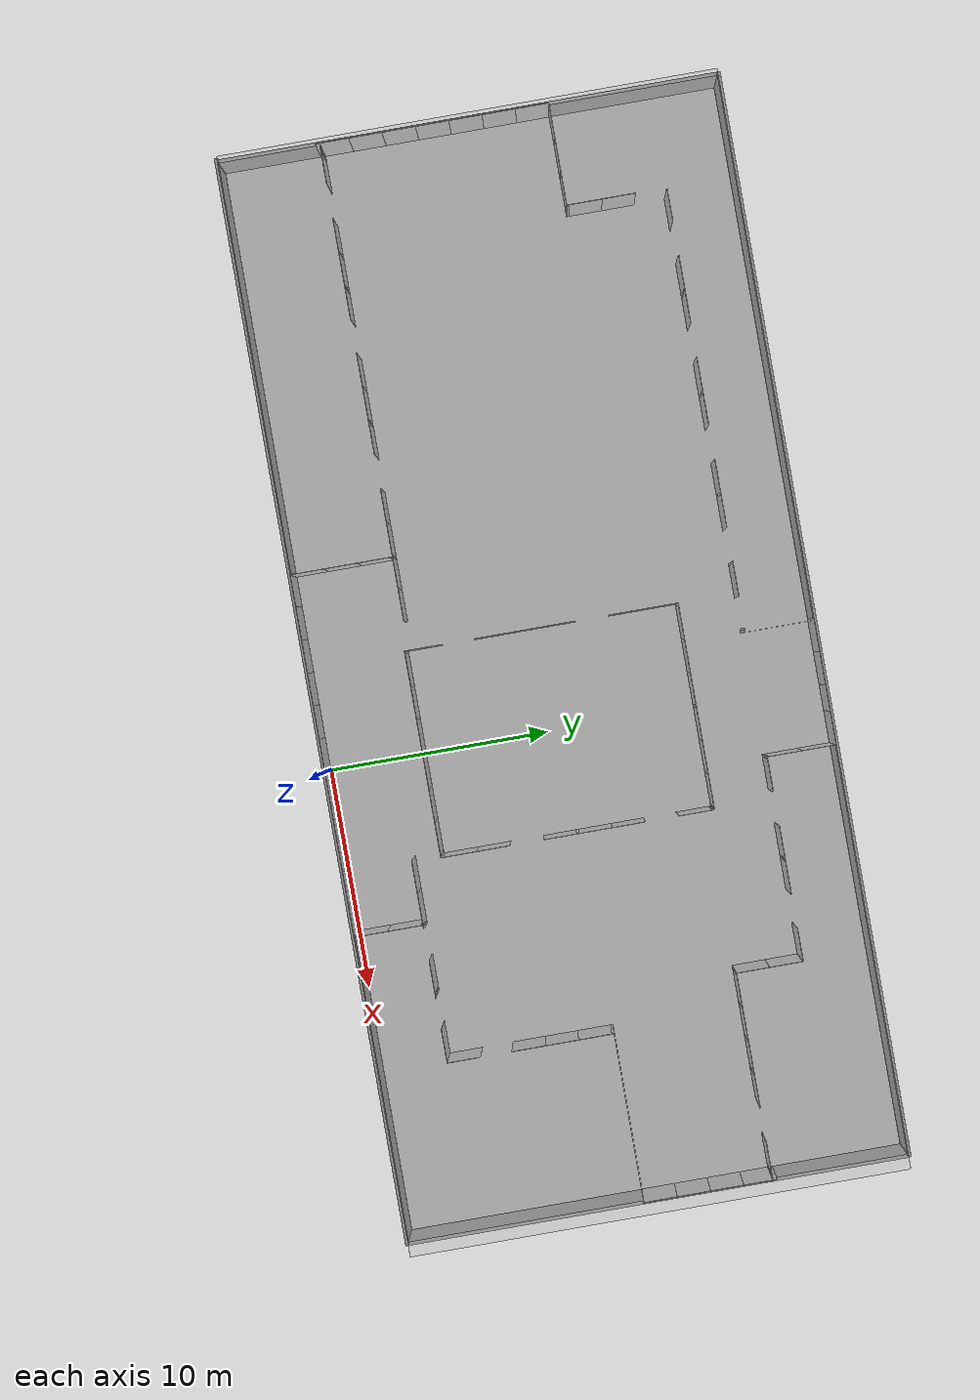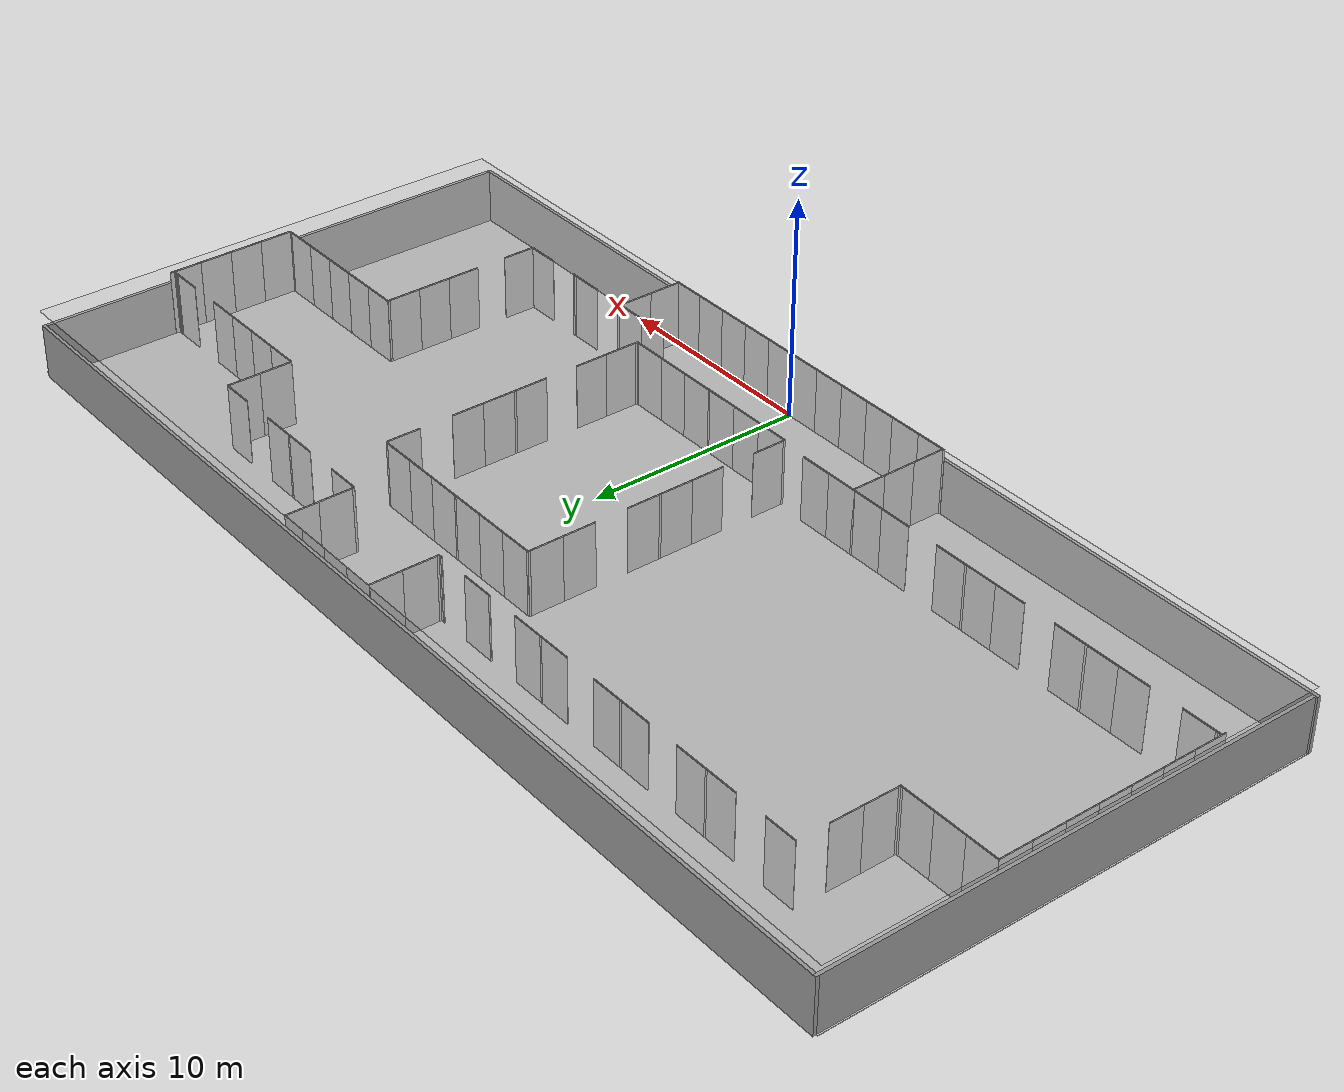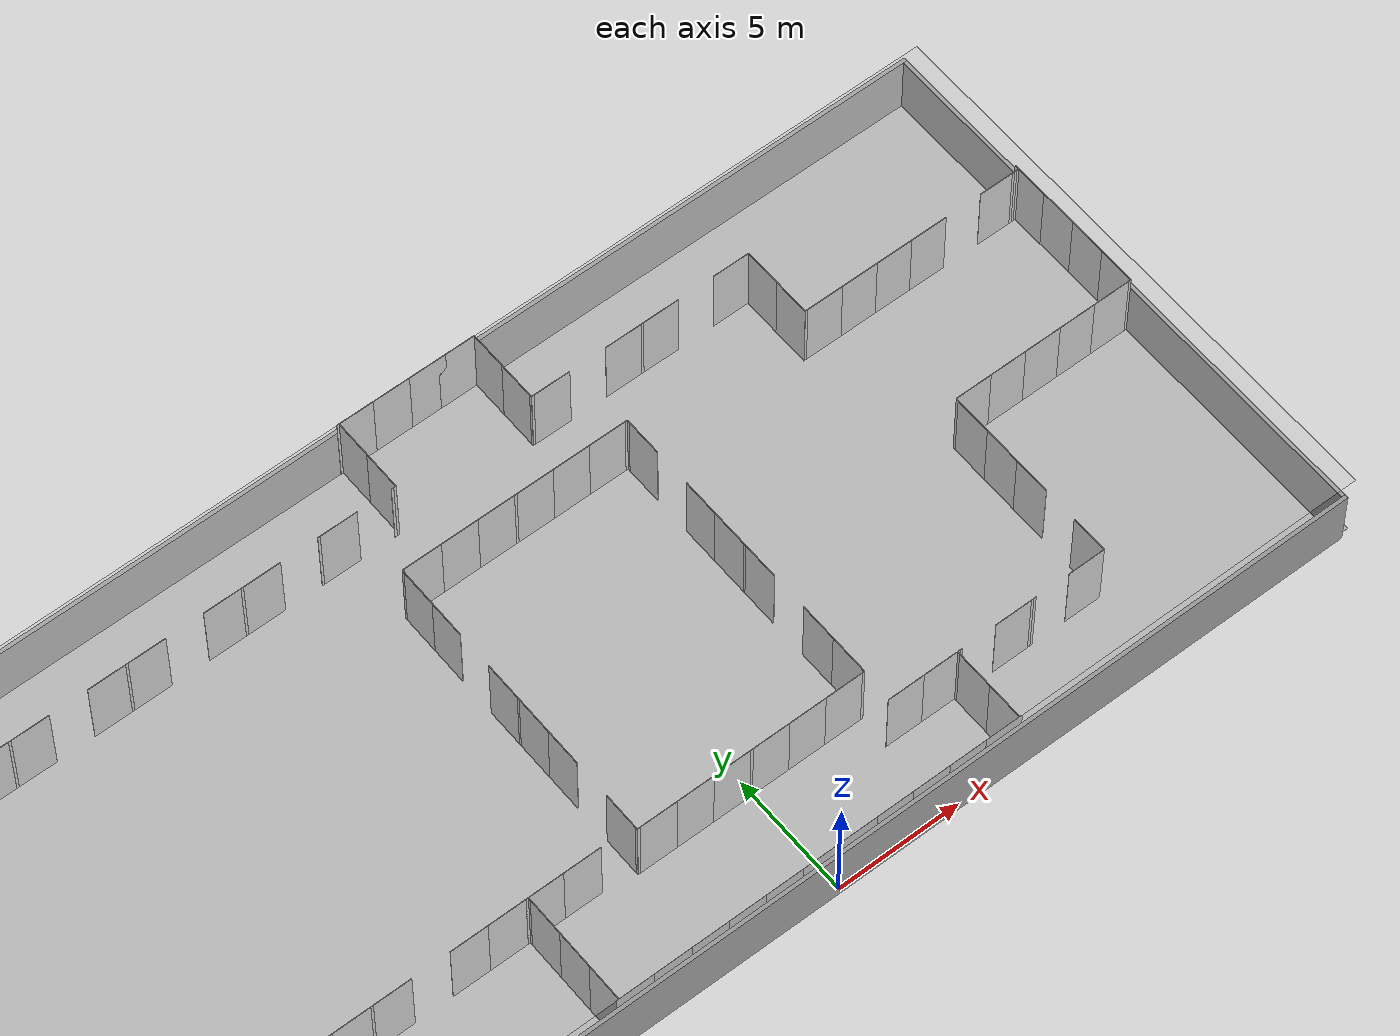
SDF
<sdf version="1.7">
 <world name="default">
  <physics type="ode">
   <real_time_update_rate>500</real_time_update_rate>
   <max_step_size>0.002</max_step_size>
   <real_time_factor>1</real_time_factor>
   <ode>
    <solver>
     <type>quick</type>
     <iters>300</iters>
     <precon_iters>0</precon_iters>
     <sor>1.4</sor>
     <use_dynamic_moi_rescaling>1</use_dynamic_moi_rescaling>
    </solver>
    <constraints>
     <cfm>0</cfm>
     <erp>0.8</erp>
     <contact_max_correcting_vel>2000</contact_max_correcting_vel>
     <contact_surface_layer>0.01</contact_surface_layer>
    </constraints>
   </ode>
  </physics>
  <scene>
   <ambient>0.8 0.8 0.8 1</ambient>
   <background>0.66 0.77 0.84 1</background>
   <grid>0</grid>
   <origin_visual>0</origin_visual>
   <shadows>1</shadows>
  </scene>
  <light name="directional_light" type="directional">
   <pose>0 0 -100 0 -0 0</pose>
   <diffuse>0.5 0.5 0.5 1</diffuse>
   <specular>0.1 0.1 0.1 1</specular>
   <direction>0.1 0.1 -0.9</direction>
   <attenuation>
    <range>20</range>
    <constant>0.5</constant>
    <linear>0.01</linear>
    <quadratic>0.001</quadratic>
   </attenuation>
   <cast_shadows>0</cast_shadows>
   <spot><inner_angle>0</inner_angle><outer_angle>0</outer_angle><falloff>0</falloff></spot>
  </light>
  <model name="ceiling">
   <pose>-2.97 11.25 3 3.14159 -0 3.14159</pose>
   <static>1</static>
   <link name="link">
    <visual name="visual">
     <geometry><plane><normal>0 0 1</normal><size>49.5 22.5</size></plane></geometry>
     <material>
      <script>
       <uri>file://media/materials/scripts/</uri>
       <uri>file://media/materials/textures/</uri>
       <name>ServiceSim/Ceiling</name>
      </script>
     </material>
    </visual>
   </link>
  </model>
  <model name="floor">
   <pose>-2.97 11.25 -0.001 0 -0 0</pose>
   <static>1</static>
   <link name="link">
    <visual name="visual">
     <geometry><plane><normal>0 0 1</normal><size>49.5 22.5</size></plane></geometry>
     <material>
      <script>
       <uri>file://media/materials/scripts/</uri>
       <uri>file://media/materials/textures/</uri>
       <name>ServiceSim/Hallway</name>
      </script>
     </material>
    </visual>
    <collision name="collision">
     <geometry><plane><normal>0 0 1</normal><size>49.5 22.5</size></plane></geometry>
     <surface><friction><ode><mu>1</mu><mu2>1</mu2></ode></friction></surface>
    </collision>
   </link>
  </model>
  <model name="walls">
   <static>1</static>
   <link name="link">
    <visual name="visual_1">
     <pose>-8.25 0 1.5 0 -0 0</pose>
     <geometry><box><size>1.5 0.01 3</size></box></geometry>
     <material>
      <script>
       <uri>file://media/materials/scripts/</uri>
       <uri>file://media/materials/textures/</uri>
       <name>ServiceSim/PlainWall</name>
      </script>
     </material>
    </visual>
    <collision name="collision_1">
     <pose>-8.25 0 1.5 0 -0 0</pose>
     <geometry><box><size>1.5 0.01 3</size></box></geometry>
    </collision>
    <visual name="visual_2">
     <pose>-6.75 0 1.5 0 -0 0</pose>
     <geometry><box><size>1.5 0.01 3</size></box></geometry>
     <material>
      <script>
       <uri>file://media/materials/scripts/</uri>
       <uri>file://media/materials/textures/</uri>
       <name>ServiceSim/PlainWall</name>
      </script>
     </material>
    </visual>
    <collision name="collision_2">
     <pose>-6.75 0 1.5 0 -0 0</pose>
     <geometry><box><size>1.5 0.01 3</size></box></geometry>
    </collision>
    <visual name="visual_3">
     <pose>-5.25 0 1.5 0 -0 0</pose>
     <geometry><box><size>1.5 0.01 3</size></box></geometry>
     <material>
      <script>
       <uri>file://media/materials/scripts/</uri>
       <uri>file://media/materials/textures/</uri>
       <name>ServiceSim/PlainWall</name>
      </script>
     </material>
    </visual>
    <collision name="collision_3">
     <pose>-5.25 0 1.5 0 -0 0</pose>
     <geometry><box><size>1.5 0.01 3</size></box></geometry>
    </collision>
    <visual name="visual_4">
     <pose>-3.75 0 1.5 0 -0 0</pose>
     <geometry><box><size>1.5 0.01 3</size></box></geometry>
     <material>
      <script>
       <uri>file://media/materials/scripts/</uri>
       <uri>file://media/materials/textures/</uri>
       <name>ServiceSim/PlainWall</name>
      </script>
     </material>
    </visual>
    <collision name="collision_4">
     <pose>-3.75 0 1.5 0 -0 0</pose>
     <geometry><box><size>1.5 0.01 3</size></box></geometry>
    </collision>
    <visual name="visual_5">
     <pose>-2.25 0 1.5 0 -0 0</pose>
     <geometry><box><size>1.5 0.01 3</size></box></geometry>
     <material>
      <script>
       <uri>file://media/materials/scripts/</uri>
       <uri>file://media/materials/textures/</uri>
       <name>ServiceSim/PlainWall</name>
      </script>
     </material>
    </visual>
    <collision name="collision_5">
     <pose>-2.25 0 1.5 0 -0 0</pose>
     <geometry><box><size>1.5 0.01 3</size></box></geometry>
    </collision>
    <visual name="visual_6">
     <pose>-0.75 0 1.5 0 -0 0</pose>
     <geometry><box><size>1.5 0.01 3</size></box></geometry>
     <material>
      <script>
       <uri>file://media/materials/scripts/</uri>
       <uri>file://media/materials/textures/</uri>
       <name>ServiceSim/Elevator</name>
      </script>
     </material>
    </visual>
    <collision name="collision_6">
     <pose>-0.75 0 1.5 0 -0 0</pose>
     <geometry><box><size>1.5 0.01 3</size></box></geometry>
    </collision>
    <visual name="visual_7">
     <pose>0.75 0 1.5 0 -0 0</pose>
     <geometry><box><size>1.5 0.01 3</size></box></geometry>
     <material>
      <script>
       <uri>file://media/materials/scripts/</uri>
       <uri>file://media/materials/textures/</uri>
       <name>ServiceSim/Elevator</name>
      </script>
     </material>
    </visual>
    <collision name="collision_7">
     <pose>0.75 0 1.5 0 -0 0</pose>
     <geometry><box><size>1.5 0.01 3</size></box></geometry>
    </collision>
    <visual name="visual_8">
     <pose>2.25 0 1.5 0 -0 0</pose>
     <geometry><box><size>1.5 0.01 3</size></box></geometry>
     <material>
      <script>
       <uri>file://media/materials/scripts/</uri>
       <uri>file://media/materials/textures/</uri>
       <name>ServiceSim/PlainWall</name>
      </script>
     </material>
    </visual>
    <collision name="collision_8">
     <pose>2.25 0 1.5 0 -0 0</pose>
     <geometry><box><size>1.5 0.01 3</size></box></geometry>
    </collision>
    <visual name="visual_9">
     <pose>3.75 0 1.5 0 -0 0</pose>
     <geometry><box><size>1.5 0.01 3</size></box></geometry>
     <material>
      <script>
       <uri>file://media/materials/scripts/</uri>
       <uri>file://media/materials/textures/</uri>
       <name>ServiceSim/PlainWall</name>
      </script>
     </material>
    </visual>
    <collision name="collision_9">
     <pose>3.75 0 1.5 0 -0 0</pose>
     <geometry><box><size>1.5 0.01 3</size></box></geometry>
    </collision>
    <visual name="visual_10">
     <pose>5.25 0 1.5 0 -0 0</pose>
     <geometry><box><size>1.5 0.01 3</size></box></geometry>
     <material>
      <script>
       <uri>file://media/materials/scripts/</uri>
       <uri>file://media/materials/textures/</uri>
       <name>ServiceSim/PlainWall</name>
      </script>
     </material>
    </visual>
    <collision name="collision_10">
     <pose>5.25 0 1.5 0 -0 0</pose>
     <geometry><box><size>1.5 0.01 3</size></box></geometry>
    </collision>
    <visual name="visual_11">
     <pose>6.749 0 1.5 0 -0 0</pose>
     <geometry><box><size>1.5 0.01 3</size></box></geometry>
     <material>
      <script>
       <uri>file://media/materials/scripts/</uri>
       <uri>file://media/materials/textures/</uri>
       <name>ServiceSim/PlainWall</name>
      </script>
     </material>
    </visual>
    <collision name="collision_11">
     <pose>6.749 0 1.5 0 -0 0</pose>
     <geometry><box><size>1.5 0.01 3</size></box></geometry>
    </collision>
    <visual name="visual_12">
     <pose>-8.25 4.6 1.5 0 -0 0</pose>
     <geometry><box><size>1.5 0.01 3</size></box></geometry>
     <material>
      <script>
       <uri>file://media/materials/scripts/</uri>
       <uri>file://media/materials/textures/</uri>
       <name>ServiceSim/PlainWall</name>
      </script>
     </material>
    </visual>
    <collision name="collision_12">
     <pose>-8.25 4.6 1.5 0 -0 0</pose>
     <geometry><box><size>1.5 0.01 3</size></box></geometry>
    </collision>
    <visual name="visual_13">
     <pose>-6.75 4.6 1.5 0 -0 0</pose>
     <geometry><box><size>1.5 0.01 3</size></box></geometry>
     <material>
      <script>
       <uri>file://media/materials/scripts/</uri>
       <uri>file://media/materials/textures/</uri>
       <name>ServiceSim/PlainWall</name>
      </script>
     </material>
    </visual>
    <collision name="collision_13">
     <pose>-6.75 4.6 1.5 0 -0 0</pose>
     <geometry><box><size>1.5 0.01 3</size></box></geometry>
    </collision>
    <visual name="visual_14">
     <pose>5.25 3.1 1.5 0 -0 0</pose>
     <geometry><box><size>1.5 0.01 3</size></box></geometry>
     <material>
      <script>
       <uri>file://media/materials/scripts/</uri>
       <uri>file://media/materials/textures/</uri>
       <name>ServiceSim/PlainWall</name>
      </script>
     </material>
    </visual>
    <collision name="collision_14">
     <pose>5.25 3.1 1.5 0 -0 0</pose>
     <geometry><box><size>1.5 0.01 3</size></box></geometry>
    </collision>
    <visual name="visual_15">
     <pose>6.75 3.1 1.5 0 -0 0</pose>
     <geometry><box><size>1.5 0.01 3</size></box></geometry>
     <material>
      <script>
       <uri>file://media/materials/scripts/</uri>
       <uri>file://media/materials/textures/</uri>
       <name>ServiceSim/PlainWall</name>
      </script>
     </material>
    </visual>
    <collision name="collision_15">
     <pose>6.75 3.1 1.5 0 -0 0</pose>
     <geometry><box><size>1.5 0.01 3</size></box></geometry>
    </collision>
    <visual name="visual_16">
     <pose>7.4 0.75 1.5 0 -0 1.5708</pose>
     <geometry><box><size>1.5 0.01 3</size></box></geometry>
     <material>
      <script>
       <uri>file://media/materials/scripts/</uri>
       <uri>file://media/materials/textures/</uri>
       <name>ServiceSim/PlainWall</name>
      </script>
     </material>
    </visual>
    <collision name="collision_16">
     <pose>7.4 0.75 1.5 0 -0 1.5708</pose>
     <geometry><box><size>1.5 0.01 3</size></box></geometry>
    </collision>
    <visual name="visual_17">
     <pose>7.4 2.25 1.5 0 -0 1.5708</pose>
     <geometry><box><size>1.5 0.01 3</size></box></geometry>
     <material>
      <script>
       <uri>file://media/materials/scripts/</uri>
       <uri>file://media/materials/textures/</uri>
       <name>ServiceSim/PlainWall</name>
      </script>
     </material>
    </visual>
    <collision name="collision_17">
     <pose>7.4 2.25 1.5 0 -0 1.5708</pose>
     <geometry><box><size>1.5 0.01 3</size></box></geometry>
    </collision>
    <visual name="visual_18">
     <pose>7.4 3.05 1.5 0 -0 1.5708</pose>
     <geometry><box><size>0.1 0.01 3</size></box></geometry>
     <material>
      <script>
       <uri>file://media/materials/scripts/</uri>
       <uri>file://media/materials/textures/</uri>
       <name>ServiceSim/PlainWall</name>
      </script>
     </material>
    </visual>
    <collision name="collision_18">
     <pose>7.4 3.05 1.5 0 -0 1.5708</pose>
     <geometry><box><size>0.1 0.01 3</size></box></geometry>
    </collision>
    <visual name="visual_19">
     <pose>7.45 3.1 1.5 0 -0 0</pose>
     <geometry><box><size>0.1 0.01 3</size></box></geometry>
     <material>
      <script>
       <uri>file://media/materials/scripts/</uri>
       <uri>file://media/materials/textures/</uri>
       <name>ServiceSim/PlainWall</name>
      </script>
     </material>
    </visual>
    <collision name="collision_19">
     <pose>7.45 3.1 1.5 0 -0 0</pose>
     <geometry><box><size>0.1 0.01 3</size></box></geometry>
    </collision>
    <visual name="visual_20">
     <pose>7.55 3.1 1.5 0 -0 0</pose>
     <geometry><box><size>0.1 0.01 3</size></box></geometry>
     <material>
      <script>
       <uri>file://media/materials/scripts/</uri>
       <uri>file://media/materials/textures/</uri>
       <name>ServiceSim/PlainWall</name>
      </script>
     </material>
    </visual>
    <collision name="collision_20">
     <pose>7.55 3.1 1.5 0 -0 0</pose>
     <geometry><box><size>0.1 0.01 3</size></box></geometry>
    </collision>
    <visual name="visual_21">
     <pose>9.75 3.1 1.5 0 -0 0</pose>
     <geometry><box><size>1.5 0.01 3</size></box></geometry>
     <material>
      <script>
       <uri>file://media/materials/scripts/</uri>
       <uri>file://media/materials/textures/</uri>
       <name>ServiceSim/PlainWall</name>
      </script>
     </material>
    </visual>
    <collision name="collision_21">
     <pose>9.75 3.1 1.5 0 -0 0</pose>
     <geometry><box><size>1.5 0.01 3</size></box></geometry>
    </collision>
    <visual name="visual_22">
     <pose>10.55 3.1 1.5 0 -0 0</pose>
     <geometry><box><size>0.1 0.01 3</size></box></geometry>
     <material>
      <script>
       <uri>file://media/materials/scripts/</uri>
       <uri>file://media/materials/textures/</uri>
       <name>ServiceSim/PlainWall</name>
      </script>
     </material>
    </visual>
    <collision name="collision_22">
     <pose>10.55 3.1 1.5 0 -0 0</pose>
     <geometry><box><size>0.1 0.01 3</size></box></geometry>
    </collision>
    <visual name="visual_23">
     <pose>10.65 3.1 1.5 0 -0 0</pose>
     <geometry><box><size>0.1 0.01 3</size></box></geometry>
     <material>
      <script>
       <uri>file://media/materials/scripts/</uri>
       <uri>file://media/materials/textures/</uri>
       <name>ServiceSim/PlainWall</name>
      </script>
     </material>
    </visual>
    <collision name="collision_23">
     <pose>10.65 3.1 1.5 0 -0 0</pose>
     <geometry><box><size>0.1 0.01 3</size></box></geometry>
    </collision>
    <visual name="visual_24">
     <pose>12.85 3.1 1.5 0 -0 0</pose>
     <geometry><box><size>1.5 0.01 3</size></box></geometry>
     <material>
      <script>
       <uri>file://media/materials/scripts/</uri>
       <uri>file://media/materials/textures/</uri>
       <name>ServiceSim/PlainWall</name>
      </script>
     </material>
    </visual>
    <collision name="collision_24">
     <pose>12.85 3.1 1.5 0 -0 0</pose>
     <geometry><box><size>1.5 0.01 3</size></box></geometry>
    </collision>
    <visual name="visual_25">
     <pose>13.6 3.85 1.5 0 -0 1.5708</pose>
     <geometry><box><size>1.5 0.01 3</size></box></geometry>
     <material>
      <script>
       <uri>file://media/materials/scripts/</uri>
       <uri>file://media/materials/textures/</uri>
       <name>ServiceSim/PlainWall</name>
      </script>
     </material>
    </visual>
    <collision name="collision_25">
     <pose>13.6 3.85 1.5 0 -0 1.5708</pose>
     <geometry><box><size>1.5 0.01 3</size></box></geometry>
    </collision>
    <visual name="visual_26">
     <pose>13.6 6.75 1.5 0 -0 1.5708</pose>
     <geometry><box><size>1.5 0.01 3</size></box></geometry>
     <material>
      <script>
       <uri>file://media/materials/scripts/</uri>
       <uri>file://media/materials/textures/</uri>
       <name>ServiceSim/PlainWall</name>
      </script>
     </material>
    </visual>
    <collision name="collision_26">
     <pose>13.6 6.75 1.5 0 -0 1.5708</pose>
     <geometry><box><size>1.5 0.01 3</size></box></geometry>
    </collision>
    <visual name="visual_27">
     <pose>13.6 8.25 1.5 0 -0 1.5708</pose>
     <geometry><box><size>1.5 0.01 3</size></box></geometry>
     <material>
      <script>
       <uri>file://media/materials/scripts/</uri>
       <uri>file://media/materials/textures/</uri>
       <name>ServiceSim/PlainWall</name>
      </script>
     </material>
    </visual>
    <collision name="collision_27">
     <pose>13.6 8.25 1.5 0 -0 1.5708</pose>
     <geometry><box><size>1.5 0.01 3</size></box></geometry>
    </collision>
    <visual name="visual_28">
     <pose>13.6 9.75 1.5 0 -0 1.5708</pose>
     <geometry><box><size>1.5 0.01 3</size></box></geometry>
     <material>
      <script>
       <uri>file://media/materials/scripts/</uri>
       <uri>file://media/materials/textures/</uri>
       <name>ServiceSim/PlainWall</name>
      </script>
     </material>
    </visual>
    <collision name="collision_28">
     <pose>13.6 9.75 1.5 0 -0 1.5708</pose>
     <geometry><box><size>1.5 0.01 3</size></box></geometry>
    </collision>
    <visual name="visual_29">
     <pose>13.6 10.55 1.5 0 -0 1.5708</pose>
     <geometry><box><size>0.1 0.01 3</size></box></geometry>
     <material>
      <script>
       <uri>file://media/materials/scripts/</uri>
       <uri>file://media/materials/textures/</uri>
       <name>ServiceSim/PlainWall</name>
      </script>
     </material>
    </visual>
    <collision name="collision_29">
     <pose>13.6 10.55 1.5 0 -0 1.5708</pose>
     <geometry><box><size>0.1 0.01 3</size></box></geometry>
    </collision>
    <visual name="visual_30">
     <pose>14.35 10.6 1.5 0 -0 0</pose>
     <geometry><box><size>1.5 0.01 3</size></box></geometry>
     <material>
      <script>
       <uri>file://media/materials/scripts/</uri>
       <uri>file://media/materials/textures/</uri>
       <name>ServiceSim/PlainWall</name>
      </script>
     </material>
    </visual>
    <collision name="collision_30">
     <pose>14.35 10.6 1.5 0 -0 0</pose>
     <geometry><box><size>1.5 0.01 3</size></box></geometry>
    </collision>
    <visual name="visual_31">
     <pose>15.85 10.6 1.5 0 -0 0</pose>
     <geometry><box><size>1.5 0.01 3</size></box></geometry>
     <material>
      <script>
       <uri>file://media/materials/scripts/</uri>
       <uri>file://media/materials/textures/</uri>
       <name>ServiceSim/PlainWall</name>
      </script>
     </material>
    </visual>
    <collision name="collision_31">
     <pose>15.85 10.6 1.5 0 -0 0</pose>
     <geometry><box><size>1.5 0.01 3</size></box></geometry>
    </collision>
    <visual name="visual_32">
     <pose>17.35 10.6 1.5 0 -0 0</pose>
     <geometry><box><size>1.5 0.01 3</size></box></geometry>
     <material>
      <script>
       <uri>file://media/materials/scripts/</uri>
       <uri>file://media/materials/textures/</uri>
       <name>ServiceSim/PlainWall</name>
      </script>
     </material>
    </visual>
    <collision name="collision_32">
     <pose>17.35 10.6 1.5 0 -0 0</pose>
     <geometry><box><size>1.5 0.01 3</size></box></geometry>
    </collision>
    <visual name="visual_33">
     <pose>18.85 10.6 1.5 0 -0 0</pose>
     <geometry><box><size>1.5 0.01 3</size></box></geometry>
     <material>
      <script>
       <uri>file://media/materials/scripts/</uri>
       <uri>file://media/materials/textures/</uri>
       <name>ServiceSim/PlainWall</name>
      </script>
     </material>
    </visual>
    <collision name="collision_33">
     <pose>18.85 10.6 1.5 0 -0 0</pose>
     <geometry><box><size>1.5 0.01 3</size></box></geometry>
    </collision>
    <visual name="visual_34">
     <pose>20.35 10.6 1.5 0 -0 0</pose>
     <geometry><box><size>1.5 0.01 3</size></box></geometry>
     <material>
      <script>
       <uri>file://media/materials/scripts/</uri>
       <uri>file://media/materials/textures/</uri>
       <name>ServiceSim/PlainWall</name>
      </script>
     </material>
    </visual>
    <collision name="collision_34">
     <pose>20.35 10.6 1.5 0 -0 0</pose>
     <geometry><box><size>1.5 0.01 3</size></box></geometry>
    </collision>
    <visual name="visual_35">
     <pose>21.15 10.6 1.5 0 -0 0</pose>
     <geometry><box><size>0.1 0.01 3</size></box></geometry>
     <material>
      <script>
       <uri>file://media/materials/scripts/</uri>
       <uri>file://media/materials/textures/</uri>
       <name>ServiceSim/PlainWall</name>
      </script>
     </material>
    </visual>
    <collision name="collision_35">
     <pose>21.15 10.6 1.5 0 -0 0</pose>
     <geometry><box><size>0.1 0.01 3</size></box></geometry>
    </collision>
    <visual name="visual_36">
     <pose>21.2 11.35 1.5 0 -0 1.5708</pose>
     <geometry><box><size>1.5 0.01 3</size></box></geometry>
     <material>
      <script>
       <uri>file://media/materials/scripts/</uri>
       <uri>file://media/materials/textures/</uri>
       <name>ServiceSim/PlainWall</name>
      </script>
     </material>
    </visual>
    <collision name="collision_36">
     <pose>21.2 11.35 1.5 0 -0 1.5708</pose>
     <geometry><box><size>1.5 0.01 3</size></box></geometry>
    </collision>
    <visual name="visual_37">
     <pose>21.2 12.85 1.5 0 -0 1.5708</pose>
     <geometry><box><size>1.5 0.01 3</size></box></geometry>
     <material>
      <script>
       <uri>file://media/materials/scripts/</uri>
       <uri>file://media/materials/textures/</uri>
       <name>ServiceSim/PlainWall</name>
      </script>
     </material>
    </visual>
    <collision name="collision_37">
     <pose>21.2 12.85 1.5 0 -0 1.5708</pose>
     <geometry><box><size>1.5 0.01 3</size></box></geometry>
    </collision>
    <visual name="visual_38">
     <pose>21.2 14.35 1.5 0 -0 1.5708</pose>
     <geometry><box><size>1.5 0.01 3</size></box></geometry>
     <material>
      <script>
       <uri>file://media/materials/scripts/</uri>
       <uri>file://media/materials/textures/</uri>
       <name>ServiceSim/PlainWall</name>
      </script>
     </material>
    </visual>
    <collision name="collision_38">
     <pose>21.2 14.35 1.5 0 -0 1.5708</pose>
     <geometry><box><size>1.5 0.01 3</size></box></geometry>
    </collision>
    <visual name="visual_39">
     <pose>21.2 15.85 1.5 0 -0 1.5708</pose>
     <geometry><box><size>1.5 0.01 3</size></box></geometry>
     <material>
      <script>
       <uri>file://media/materials/scripts/</uri>
       <uri>file://media/materials/textures/</uri>
       <name>ServiceSim/PlainWall</name>
      </script>
     </material>
    </visual>
    <collision name="collision_39">
     <pose>21.2 15.85 1.5 0 -0 1.5708</pose>
     <geometry><box><size>1.5 0.01 3</size></box></geometry>
    </collision>
    <visual name="visual_40">
     <pose>20.95 16.4 1.5 0 -0 0</pose>
     <geometry><box><size>0.1 0.01 3</size></box></geometry>
     <material>
      <script>
       <uri>file://media/materials/scripts/</uri>
       <uri>file://media/materials/textures/</uri>
       <name>ServiceSim/PlainWall</name>
      </script>
     </material>
    </visual>
    <collision name="collision_40">
     <pose>20.95 16.4 1.5 0 -0 0</pose>
     <geometry><box><size>0.1 0.01 3</size></box></geometry>
    </collision>
    <visual name="visual_41">
     <pose>21.05 16.4 1.5 0 -0 0</pose>
     <geometry><box><size>0.1 0.01 3</size></box></geometry>
     <material>
      <script>
       <uri>file://media/materials/scripts/</uri>
       <uri>file://media/materials/textures/</uri>
       <name>ServiceSim/PlainWall</name>
      </script>
     </material>
    </visual>
    <collision name="collision_41">
     <pose>21.05 16.4 1.5 0 -0 0</pose>
     <geometry><box><size>0.1 0.01 3</size></box></geometry>
    </collision>
    <visual name="visual_42">
     <pose>21.15 16.4 1.5 0 -0 0</pose>
     <geometry><box><size>0.1 0.01 3</size></box></geometry>
     <material>
      <script>
       <uri>file://media/materials/scripts/</uri>
       <uri>file://media/materials/textures/</uri>
       <name>ServiceSim/PlainWall</name>
      </script>
     </material>
    </visual>
    <collision name="collision_42">
     <pose>21.15 16.4 1.5 0 -0 0</pose>
     <geometry><box><size>0.1 0.01 3</size></box></geometry>
    </collision>
    <visual name="visual_43">
     <pose>20.25 16.4 1.5 0 -0 0</pose>
     <geometry><box><size>1.5 0.01 3</size></box></geometry>
     <material>
      <script>
       <uri>file://media/materials/scripts/</uri>
       <uri>file://media/materials/textures/</uri>
       <name>ServiceSim/PlainWall</name>
      </script>
     </material>
    </visual>
    <collision name="collision_43">
     <pose>20.25 16.4 1.5 0 -0 0</pose>
     <geometry><box><size>1.5 0.01 3</size></box></geometry>
    </collision>
    <visual name="visual_44">
     <pose>17.25 16.4 1.5 0 -0 0</pose>
     <geometry><box><size>1.5 0.01 3</size></box></geometry>
     <material>
      <script>
       <uri>file://media/materials/scripts/</uri>
       <uri>file://media/materials/textures/</uri>
       <name>ServiceSim/PlainWall</name>
      </script>
     </material>
    </visual>
    <collision name="collision_44">
     <pose>17.25 16.4 1.5 0 -0 0</pose>
     <geometry><box><size>1.5 0.01 3</size></box></geometry>
    </collision>
    <visual name="visual_45">
     <pose>15.75 16.4 1.5 0 -0 0</pose>
     <geometry><box><size>1.5 0.01 3</size></box></geometry>
     <material>
      <script>
       <uri>file://media/materials/scripts/</uri>
       <uri>file://media/materials/textures/</uri>
       <name>ServiceSim/PlainWall</name>
      </script>
     </material>
    </visual>
    <collision name="collision_45">
     <pose>15.75 16.4 1.5 0 -0 0</pose>
     <geometry><box><size>1.5 0.01 3</size></box></geometry>
    </collision>
    <visual name="visual_46">
     <pose>14.25 16.4 1.5 0 -0 0</pose>
     <geometry><box><size>1.5 0.01 3</size></box></geometry>
     <material>
      <script>
       <uri>file://media/materials/scripts/</uri>
       <uri>file://media/materials/textures/</uri>
       <name>ServiceSim/PlainWall</name>
      </script>
     </material>
    </visual>
    <collision name="collision_46">
     <pose>14.25 16.4 1.5 0 -0 0</pose>
     <geometry><box><size>1.5 0.01 3</size></box></geometry>
    </collision>
    <visual name="visual_47">
     <pose>12.75 16.4 1.5 0 -0 0</pose>
     <geometry><box><size>1.5 0.01 3</size></box></geometry>
     <material>
      <script>
       <uri>file://media/materials/scripts/</uri>
       <uri>file://media/materials/textures/</uri>
       <name>ServiceSim/PlainWall</name>
      </script>
     </material>
    </visual>
    <collision name="collision_47">
     <pose>12.75 16.4 1.5 0 -0 0</pose>
     <geometry><box><size>1.5 0.01 3</size></box></geometry>
    </collision>
    <visual name="visual_48">
     <pose>11.95 16.4 1.5 0 -0 0</pose>
     <geometry><box><size>0.1 0.01 3</size></box></geometry>
     <material>
      <script>
       <uri>file://media/materials/scripts/</uri>
       <uri>file://media/materials/textures/</uri>
       <name>ServiceSim/PlainWall</name>
      </script>
     </material>
    </visual>
    <collision name="collision_48">
     <pose>11.95 16.4 1.5 0 -0 0</pose>
     <geometry><box><size>0.1 0.01 3</size></box></geometry>
    </collision>
    <visual name="visual_49">
     <pose>11.9 17.15 1.5 0 -0 1.5708</pose>
     <geometry><box><size>1.5 0.01 3</size></box></geometry>
     <material>
      <script>
       <uri>file://media/materials/scripts/</uri>
       <uri>file://media/materials/textures/</uri>
       <name>ServiceSim/PlainWall</name>
      </script>
     </material>
    </visual>
    <collision name="collision_49">
     <pose>11.9 17.15 1.5 0 -0 1.5708</pose>
     <geometry><box><size>1.5 0.01 3</size></box></geometry>
    </collision>
    <visual name="visual_50">
     <pose>11.9 18.65 1.5 0 -0 1.5708</pose>
     <geometry><box><size>1.5 0.01 3</size></box></geometry>
     <material>
      <script>
       <uri>file://media/materials/scripts/</uri>
       <uri>file://media/materials/textures/</uri>
       <name>ServiceSim/PlainWall</name>
      </script>
     </material>
    </visual>
    <collision name="collision_50">
     <pose>11.9 18.65 1.5 0 -0 1.5708</pose>
     <geometry><box><size>1.5 0.01 3</size></box></geometry>
    </collision>
    <visual name="visual_51">
     <pose>11.15 19.4 1.5 0 -0 0</pose>
     <geometry><box><size>1.5 0.01 3</size></box></geometry>
     <material>
      <script>
       <uri>file://media/materials/scripts/</uri>
       <uri>file://media/materials/textures/</uri>
       <name>ServiceSim/PlainWall</name>
      </script>
     </material>
    </visual>
    <collision name="collision_51">
     <pose>11.15 19.4 1.5 0 -0 0</pose>
     <geometry><box><size>1.5 0.01 3</size></box></geometry>
    </collision>
    <visual name="visual_52">
     <pose>8.15 19.4 1.5 0 -0 0</pose>
     <geometry><box><size>1.5 0.01 3</size></box></geometry>
     <material>
      <script>
       <uri>file://media/materials/scripts/</uri>
       <uri>file://media/materials/textures/</uri>
       <name>ServiceSim/PlainWall</name>
      </script>
     </material>
    </visual>
    <collision name="collision_52">
     <pose>8.15 19.4 1.5 0 -0 0</pose>
     <geometry><box><size>1.5 0.01 3</size></box></geometry>
    </collision>
    <visual name="visual_53">
     <pose>7.35 19.4 1.5 0 -0 0</pose>
     <geometry><box><size>0.1 0.01 3</size></box></geometry>
     <material>
      <script>
       <uri>file://media/materials/scripts/</uri>
       <uri>file://media/materials/textures/</uri>
       <name>ServiceSim/PlainWall</name>
      </script>
     </material>
    </visual>
    <collision name="collision_53">
     <pose>7.35 19.4 1.5 0 -0 0</pose>
     <geometry><box><size>0.1 0.01 3</size></box></geometry>
    </collision>
    <visual name="visual_54">
     <pose>6.55 19.4 1.5 0 -0 0</pose>
     <geometry><box><size>1.5 0.01 3</size></box></geometry>
     <material>
      <script>
       <uri>file://media/materials/scripts/</uri>
       <uri>file://media/materials/textures/</uri>
       <name>ServiceSim/PlainWall</name>
      </script>
     </material>
    </visual>
    <collision name="collision_54">
     <pose>6.55 19.4 1.5 0 -0 0</pose>
     <geometry><box><size>1.5 0.01 3</size></box></geometry>
    </collision>
    <visual name="visual_55">
     <pose>3.55 19.4 1.5 0 -0 0</pose>
     <geometry><box><size>1.5 0.01 3</size></box></geometry>
     <material>
      <script>
       <uri>file://media/materials/scripts/</uri>
       <uri>file://media/materials/textures/</uri>
       <name>ServiceSim/PlainWall</name>
      </script>
     </material>
    </visual>
    <collision name="collision_55">
     <pose>3.55 19.4 1.5 0 -0 0</pose>
     <geometry><box><size>1.5 0.01 3</size></box></geometry>
    </collision>
    <visual name="visual_56">
     <pose>2.75 19.4 1.5 0 -0 0</pose>
     <geometry><box><size>0.1 0.01 3</size></box></geometry>
     <material>
      <script>
       <uri>file://media/materials/scripts/</uri>
       <uri>file://media/materials/textures/</uri>
       <name>ServiceSim/PlainWall</name>
      </script>
     </material>
    </visual>
    <collision name="collision_56">
     <pose>2.75 19.4 1.5 0 -0 0</pose>
     <geometry><box><size>0.1 0.01 3</size></box></geometry>
    </collision>
    <visual name="visual_57">
     <pose>2.7 19.45 1.5 0 -0 1.5708</pose>
     <geometry><box><size>0.1 0.01 3</size></box></geometry>
     <material>
      <script>
       <uri>file://media/materials/scripts/</uri>
       <uri>file://media/materials/textures/</uri>
       <name>ServiceSim/PlainWall</name>
      </script>
     </material>
    </visual>
    <collision name="collision_57">
     <pose>2.7 19.45 1.5 0 -0 1.5708</pose>
     <geometry><box><size>0.1 0.01 3</size></box></geometry>
    </collision>
    <visual name="visual_58">
     <pose>2.7 20.25 1.5 0 -0 1.5708</pose>
     <geometry><box><size>1.5 0.01 3</size></box></geometry>
     <material>
      <script>
       <uri>file://media/materials/scripts/</uri>
       <uri>file://media/materials/textures/</uri>
       <name>ServiceSim/PlainWall</name>
      </script>
     </material>
    </visual>
    <collision name="collision_58">
     <pose>2.7 20.25 1.5 0 -0 1.5708</pose>
     <geometry><box><size>1.5 0.01 3</size></box></geometry>
    </collision>
    <visual name="visual_59">
     <pose>2.7 21.75 1.5 0 -0 1.5708</pose>
     <geometry><box><size>1.5 0.01 3</size></box></geometry>
     <material>
      <script>
       <uri>file://media/materials/scripts/</uri>
       <uri>file://media/materials/textures/</uri>
       <name>ServiceSim/PlainWall</name>
      </script>
     </material>
    </visual>
    <collision name="collision_59">
     <pose>2.7 21.75 1.5 0 -0 1.5708</pose>
     <geometry><box><size>1.5 0.01 3</size></box></geometry>
    </collision>
    <visual name="visual_60">
     <pose>1.95 22.5 1.5 0 -0 0</pose>
     <geometry><box><size>1.5 0.01 3</size></box></geometry>
     <material>
      <script>
       <uri>file://media/materials/scripts/</uri>
       <uri>file://media/materials/textures/</uri>
       <name>ServiceSim/PlainWall</name>
      </script>
     </material>
    </visual>
    <collision name="collision_60">
     <pose>1.95 22.5 1.5 0 -0 0</pose>
     <geometry><box><size>1.5 0.01 3</size></box></geometry>
    </collision>
    <visual name="visual_61">
     <pose>0.75 22.5 1.5 0 -0 0</pose>
     <geometry><box><size>1.5 0.01 3</size></box></geometry>
     <material>
      <script>
       <uri>file://media/materials/scripts/</uri>
       <uri>file://media/materials/textures/</uri>
       <name>ServiceSim/PlainWall</name>
      </script>
     </material>
    </visual>
    <collision name="collision_61">
     <pose>0.75 22.5 1.5 0 -0 0</pose>
     <geometry><box><size>1.5 0.01 3</size></box></geometry>
    </collision>
    <visual name="visual_62">
     <pose>-0.75 22.5 1.5 0 -0 0</pose>
     <geometry><box><size>1.5 0.01 3</size></box></geometry>
     <material>
      <script>
       <uri>file://media/materials/scripts/</uri>
       <uri>file://media/materials/textures/</uri>
       <name>ServiceSim/PlainWall</name>
      </script>
     </material>
    </visual>
    <collision name="collision_62">
     <pose>-0.75 22.5 1.5 0 -0 0</pose>
     <geometry><box><size>1.5 0.01 3</size></box></geometry>
    </collision>
    <visual name="visual_63">
     <pose>-2.25 22.5 1.5 0 -0 0</pose>
     <geometry><box><size>1.5 0.01 3</size></box></geometry>
     <material>
      <script>
       <uri>file://media/materials/scripts/</uri>
       <uri>file://media/materials/textures/</uri>
       <name>ServiceSim/Door</name>
      </script>
     </material>
    </visual>
    <collision name="collision_63">
     <pose>-2.25 22.5 1.5 0 -0 0</pose>
     <geometry><box><size>1.5 0.01 3</size></box></geometry>
    </collision>
    <visual name="visual_64">
     <pose>-2.9 21.75 1.5 0 -0 1.5708</pose>
     <geometry><box><size>1.5 0.01 3</size></box></geometry>
     <material>
      <script>
       <uri>file://media/materials/scripts/</uri>
       <uri>file://media/materials/textures/</uri>
       <name>ServiceSim/PlainWall</name>
      </script>
     </material>
    </visual>
    <collision name="collision_64">
     <pose>-2.9 21.75 1.5 0 -0 1.5708</pose>
     <geometry><box><size>1.5 0.01 3</size></box></geometry>
    </collision>
    <visual name="visual_65">
     <pose>-2.9 20.25 1.5 0 -0 1.5708</pose>
     <geometry><box><size>1.5 0.01 3</size></box></geometry>
     <material>
      <script>
       <uri>file://media/materials/scripts/</uri>
       <uri>file://media/materials/textures/</uri>
       <name>ServiceSim/PlainWall</name>
      </script>
     </material>
    </visual>
    <collision name="collision_65">
     <pose>-2.9 20.25 1.5 0 -0 1.5708</pose>
     <geometry><box><size>1.5 0.01 3</size></box></geometry>
    </collision>
    <visual name="visual_66">
     <pose>-2.9 19.45 1.5 0 -0 1.5708</pose>
     <geometry><box><size>0.1 0.01 3</size></box></geometry>
     <material>
      <script>
       <uri>file://media/materials/scripts/</uri>
       <uri>file://media/materials/textures/</uri>
       <name>ServiceSim/PlainWall</name>
      </script>
     </material>
    </visual>
    <collision name="collision_66">
     <pose>-2.9 19.45 1.5 0 -0 1.5708</pose>
     <geometry><box><size>0.1 0.01 3</size></box></geometry>
    </collision>
    <visual name="visual_67">
     <pose>-2.95 19.4 1.5 0 -0 0</pose>
     <geometry><box><size>0.1 0.01 3</size></box></geometry>
     <material>
      <script>
       <uri>file://media/materials/scripts/</uri>
       <uri>file://media/materials/textures/</uri>
       <name>ServiceSim/PlainWall</name>
      </script>
     </material>
    </visual>
    <collision name="collision_67">
     <pose>-2.95 19.4 1.5 0 -0 0</pose>
     <geometry><box><size>0.1 0.01 3</size></box></geometry>
    </collision>
    <visual name="visual_68">
     <pose>-3.05 19.4 1.5 0 -0 0</pose>
     <geometry><box><size>0.1 0.01 3</size></box></geometry>
     <material>
      <script>
       <uri>file://media/materials/scripts/</uri>
       <uri>file://media/materials/textures/</uri>
       <name>ServiceSim/PlainWall</name>
      </script>
     </material>
    </visual>
    <collision name="collision_68">
     <pose>-3.05 19.4 1.5 0 -0 0</pose>
     <geometry><box><size>0.1 0.01 3</size></box></geometry>
    </collision>
    <visual name="visual_69">
     <pose>-5.25 19.4 1.5 0 -0 0</pose>
     <geometry><box><size>1.5 0.01 3</size></box></geometry>
     <material>
      <script>
       <uri>file://media/materials/scripts/</uri>
       <uri>file://media/materials/textures/</uri>
       <name>ServiceSim/PlainWall</name>
      </script>
     </material>
    </visual>
    <collision name="collision_69">
     <pose>-5.25 19.4 1.5 0 -0 0</pose>
     <geometry><box><size>1.5 0.01 3</size></box></geometry>
    </collision>
    <visual name="visual_70">
     <pose>-6.05 19.4 1.5 0 -0 0</pose>
     <geometry><box><size>0.1 0.01 3</size></box></geometry>
     <material>
      <script>
       <uri>file://media/materials/scripts/</uri>
       <uri>file://media/materials/textures/</uri>
       <name>ServiceSim/PlainWall</name>
      </script>
     </material>
    </visual>
    <collision name="collision_70">
     <pose>-6.05 19.4 1.5 0 -0 0</pose>
     <geometry><box><size>0.1 0.01 3</size></box></geometry>
    </collision>
    <visual name="visual_71">
     <pose>-8.35 19.4 1.5 0 -0 0</pose>
     <geometry><box><size>1.5 0.01 3</size></box></geometry>
     <material>
      <script>
       <uri>file://media/materials/scripts/</uri>
       <uri>file://media/materials/textures/</uri>
       <name>ServiceSim/PlainWall</name>
      </script>
     </material>
    </visual>
    <collision name="collision_71">
     <pose>-8.35 19.4 1.5 0 -0 0</pose>
     <geometry><box><size>1.5 0.01 3</size></box></geometry>
    </collision>
    <visual name="visual_72">
     <pose>-9.15 19.4 1.5 0 -0 0</pose>
     <geometry><box><size>0.1 0.01 3</size></box></geometry>
     <material>
      <script>
       <uri>file://media/materials/scripts/</uri>
       <uri>file://media/materials/textures/</uri>
       <name>ServiceSim/PlainWall</name>
      </script>
     </material>
    </visual>
    <collision name="collision_72">
     <pose>-9.15 19.4 1.5 0 -0 0</pose>
     <geometry><box><size>0.1 0.01 3</size></box></geometry>
    </collision>
    <visual name="visual_73">
     <pose>-9.95 19.4 1.5 0 -0 0</pose>
     <geometry><box><size>1.5 0.01 3</size></box></geometry>
     <material>
      <script>
       <uri>file://media/materials/scripts/</uri>
       <uri>file://media/materials/textures/</uri>
       <name>ServiceSim/PlainWall</name>
      </script>
     </material>
    </visual>
    <collision name="collision_73">
     <pose>-9.95 19.4 1.5 0 -0 0</pose>
     <geometry><box><size>1.5 0.01 3</size></box></geometry>
    </collision>
    <visual name="visual_74">
     <pose>-12.95 19.4 1.5 0 -0 0</pose>
     <geometry><box><size>1.5 0.01 3</size></box></geometry>
     <material>
      <script>
       <uri>file://media/materials/scripts/</uri>
       <uri>file://media/materials/textures/</uri>
       <name>ServiceSim/PlainWall</name>
      </script>
     </material>
    </visual>
    <collision name="collision_74">
     <pose>-12.95 19.4 1.5 0 -0 0</pose>
     <geometry><box><size>1.5 0.01 3</size></box></geometry>
    </collision>
    <visual name="visual_75">
     <pose>-13.75 19.4 1.5 0 -0 0</pose>
     <geometry><box><size>0.1 0.01 3</size></box></geometry>
     <material>
      <script>
       <uri>file://media/materials/scripts/</uri>
       <uri>file://media/materials/textures/</uri>
       <name>ServiceSim/PlainWall</name>
      </script>
     </material>
    </visual>
    <collision name="collision_75">
     <pose>-13.75 19.4 1.5 0 -0 0</pose>
     <geometry><box><size>0.1 0.01 3</size></box></geometry>
    </collision>
    <visual name="visual_76">
     <pose>-14.55 19.4 1.5 0 -0 0</pose>
     <geometry><box><size>1.5 0.01 3</size></box></geometry>
     <material>
      <script>
       <uri>file://media/materials/scripts/</uri>
       <uri>file://media/materials/textures/</uri>
       <name>ServiceSim/PlainWall</name>
      </script>
     </material>
    </visual>
    <collision name="collision_76">
     <pose>-14.55 19.4 1.5 0 -0 0</pose>
     <geometry><box><size>1.5 0.01 3</size></box></geometry>
    </collision>
    <visual name="visual_77">
     <pose>-18.35 19.4 1.5 0 -0 0</pose>
     <geometry><box><size>0.1 0.01 3</size></box></geometry>
     <material>
      <script>
       <uri>file://media/materials/scripts/</uri>
       <uri>file://media/materials/textures/</uri>
       <name>ServiceSim/PlainWall</name>
      </script>
     </material>
    </visual>
    <collision name="collision_77">
     <pose>-18.35 19.4 1.5 0 -0 0</pose>
     <geometry><box><size>0.1 0.01 3</size></box></geometry>
    </collision>
    <visual name="visual_78">
     <pose>-17.55 19.4 1.5 0 -0 0</pose>
     <geometry><box><size>1.5 0.01 3</size></box></geometry>
     <material>
      <script>
       <uri>file://media/materials/scripts/</uri>
       <uri>file://media/materials/textures/</uri>
       <name>ServiceSim/PlainWall</name>
      </script>
     </material>
    </visual>
    <collision name="collision_78">
     <pose>-17.55 19.4 1.5 0 -0 0</pose>
     <geometry><box><size>1.5 0.01 3</size></box></geometry>
    </collision>
    <visual name="visual_79">
     <pose>-19.15 19.4 1.5 0 -0 0</pose>
     <geometry><box><size>1.5 0.01 3</size></box></geometry>
     <material>
      <script>
       <uri>file://media/materials/scripts/</uri>
       <uri>file://media/materials/textures/</uri>
       <name>ServiceSim/PlainWall</name>
      </script>
     </material>
    </visual>
    <collision name="collision_79">
     <pose>-19.15 19.4 1.5 0 -0 0</pose>
     <geometry><box><size>1.5 0.01 3</size></box></geometry>
    </collision>
    <visual name="visual_80">
     <pose>-22.15 19.4 1.5 0 -0 0</pose>
     <geometry><box><size>1.5 0.01 3</size></box></geometry>
     <material>
      <script>
       <uri>file://media/materials/scripts/</uri>
       <uri>file://media/materials/textures/</uri>
       <name>ServiceSim/PlainWall</name>
      </script>
     </material>
    </visual>
    <collision name="collision_80">
     <pose>-22.15 19.4 1.5 0 -0 0</pose>
     <geometry><box><size>1.5 0.01 3</size></box></geometry>
    </collision>
    <visual name="visual_81">
     <pose>-22.9 17.25 1.5 0 -0 1.5708</pose>
     <geometry><box><size>1.5 0.01 3</size></box></geometry>
     <material>
      <script>
       <uri>file://media/materials/scripts/</uri>
       <uri>file://media/materials/textures/</uri>
       <name>ServiceSim/PlainWall</name>
      </script>
     </material>
    </visual>
    <collision name="collision_81">
     <pose>-22.9 17.25 1.5 0 -0 1.5708</pose>
     <geometry><box><size>1.5 0.01 3</size></box></geometry>
    </collision>
    <visual name="visual_82">
     <pose>-22.9 15.75 1.5 0 -0 1.5708</pose>
     <geometry><box><size>1.5 0.01 3</size></box></geometry>
     <material>
      <script>
       <uri>file://media/materials/scripts/</uri>
       <uri>file://media/materials/textures/</uri>
       <name>ServiceSim/PlainWall</name>
      </script>
     </material>
    </visual>
    <collision name="collision_82">
     <pose>-22.9 15.75 1.5 0 -0 1.5708</pose>
     <geometry><box><size>1.5 0.01 3</size></box></geometry>
    </collision>
    <visual name="visual_83">
     <pose>-22.9 14.95 1.5 0 -0 1.5708</pose>
     <geometry><box><size>0.1 0.01 3</size></box></geometry>
     <material>
      <script>
       <uri>file://media/materials/scripts/</uri>
       <uri>file://media/materials/textures/</uri>
       <name>ServiceSim/PlainWall</name>
      </script>
     </material>
    </visual>
    <collision name="collision_83">
     <pose>-22.9 14.95 1.5 0 -0 1.5708</pose>
     <geometry><box><size>0.1 0.01 3</size></box></geometry>
    </collision>
    <visual name="visual_84">
     <pose>-22.95 14.9 1.5 0 -0 0</pose>
     <geometry><box><size>0.1 0.01 3</size></box></geometry>
     <material>
      <script>
       <uri>file://media/materials/scripts/</uri>
       <uri>file://media/materials/textures/</uri>
       <name>ServiceSim/PlainWall</name>
      </script>
     </material>
    </visual>
    <collision name="collision_84">
     <pose>-22.95 14.9 1.5 0 -0 0</pose>
     <geometry><box><size>0.1 0.01 3</size></box></geometry>
    </collision>
    <visual name="visual_85">
     <pose>-23.75 14.9 1.5 0 -0 0</pose>
     <geometry><box><size>1.5 0.01 3</size></box></geometry>
     <material>
      <script>
       <uri>file://media/materials/scripts/</uri>
       <uri>file://media/materials/textures/</uri>
       <name>ServiceSim/PlainWall</name>
      </script>
     </material>
    </visual>
    <collision name="collision_85">
     <pose>-23.75 14.9 1.5 0 -0 0</pose>
     <geometry><box><size>1.5 0.01 3</size></box></geometry>
    </collision>
    <visual name="visual_86">
     <pose>-25.25 14.9 1.5 0 -0 0</pose>
     <geometry><box><size>1.5 0.01 3</size></box></geometry>
     <material>
      <script>
       <uri>file://media/materials/scripts/</uri>
       <uri>file://media/materials/textures/</uri>
       <name>ServiceSim/PlainWall</name>
      </script>
     </material>
    </visual>
    <collision name="collision_86">
     <pose>-25.25 14.9 1.5 0 -0 0</pose>
     <geometry><box><size>1.5 0.01 3</size></box></geometry>
    </collision>
    <visual name="visual_87">
     <pose>-26.75 14.9 1.5 0 -0 0</pose>
     <geometry><box><size>1.5 0.01 3</size></box></geometry>
     <material>
      <script>
       <uri>file://media/materials/scripts/</uri>
       <uri>file://media/materials/textures/</uri>
       <name>ServiceSim/PlainWall</name>
      </script>
     </material>
    </visual>
    <collision name="collision_87">
     <pose>-26.75 14.9 1.5 0 -0 0</pose>
     <geometry><box><size>1.5 0.01 3</size></box></geometry>
    </collision>
    <visual name="visual_88">
     <pose>-27.5 14.15 1.5 0 -0 1.5708</pose>
     <geometry><box><size>1.5 0.01 3</size></box></geometry>
     <material>
      <script>
       <uri>file://media/materials/scripts/</uri>
       <uri>file://media/materials/textures/</uri>
       <name>ServiceSim/PlainWall</name>
      </script>
     </material>
    </visual>
    <collision name="collision_88">
     <pose>-27.5 14.15 1.5 0 -0 1.5708</pose>
     <geometry><box><size>1.5 0.01 3</size></box></geometry>
    </collision>
    <visual name="visual_89">
     <pose>-27.5 12.65 1.5 0 -0 1.5708</pose>
     <geometry><box><size>1.5 0.01 3</size></box></geometry>
     <material>
      <script>
       <uri>file://media/materials/scripts/</uri>
       <uri>file://media/materials/textures/</uri>
       <name>ServiceSim/PlainWall</name>
      </script>
     </material>
    </visual>
    <collision name="collision_89">
     <pose>-27.5 12.65 1.5 0 -0 1.5708</pose>
     <geometry><box><size>1.5 0.01 3</size></box></geometry>
    </collision>
    <visual name="visual_90">
     <pose>-27.5 11.15 1.5 0 -0 1.5708</pose>
     <geometry><box><size>1.5 0.01 3</size></box></geometry>
     <material>
      <script>
       <uri>file://media/materials/scripts/</uri>
       <uri>file://media/materials/textures/</uri>
       <name>ServiceSim/PlainWall</name>
      </script>
     </material>
    </visual>
    <collision name="collision_90">
     <pose>-27.5 11.15 1.5 0 -0 1.5708</pose>
     <geometry><box><size>1.5 0.01 3</size></box></geometry>
    </collision>
    <visual name="visual_91">
     <pose>-27.5 9.65 1.5 0 -0 1.5708</pose>
     <geometry><box><size>1.5 0.01 3</size></box></geometry>
     <material>
      <script>
       <uri>file://media/materials/scripts/</uri>
       <uri>file://media/materials/textures/</uri>
       <name>ServiceSim/PlainWall</name>
      </script>
     </material>
    </visual>
    <collision name="collision_91">
     <pose>-27.5 9.65 1.5 0 -0 1.5708</pose>
     <geometry><box><size>1.5 0.01 3</size></box></geometry>
    </collision>
    <visual name="visual_92">
     <pose>-27.5 8.15 1.5 0 -0 1.5708</pose>
     <geometry><box><size>1.5 0.01 3</size></box></geometry>
     <material>
      <script>
       <uri>file://media/materials/scripts/</uri>
       <uri>file://media/materials/textures/</uri>
       <name>ServiceSim/PlainWall</name>
      </script>
     </material>
    </visual>
    <collision name="collision_92">
     <pose>-27.5 8.15 1.5 0 -0 1.5708</pose>
     <geometry><box><size>1.5 0.01 3</size></box></geometry>
    </collision>
    <visual name="visual_93">
     <pose>-27.5 6.65 1.5 0 -0 1.5708</pose>
     <geometry><box><size>1.5 0.01 3</size></box></geometry>
     <material>
      <script>
       <uri>file://media/materials/scripts/</uri>
       <uri>file://media/materials/textures/</uri>
       <name>ServiceSim/PlainWall</name>
      </script>
     </material>
    </visual>
    <collision name="collision_93">
     <pose>-27.5 6.65 1.5 0 -0 1.5708</pose>
     <geometry><box><size>1.5 0.01 3</size></box></geometry>
    </collision>
    <visual name="visual_94">
     <pose>-27.5 5.15 1.5 0 -0 1.5708</pose>
     <geometry><box><size>1.5 0.01 3</size></box></geometry>
     <material>
      <script>
       <uri>file://media/materials/scripts/</uri>
       <uri>file://media/materials/textures/</uri>
       <name>ServiceSim/PlainWall</name>
      </script>
     </material>
    </visual>
    <collision name="collision_94">
     <pose>-27.5 5.15 1.5 0 -0 1.5708</pose>
     <geometry><box><size>1.5 0.01 3</size></box></geometry>
    </collision>
    <visual name="visual_95">
     <pose>-27.45 4.6 1.5 0 -0 0</pose>
     <geometry><box><size>0.1 0.01 3</size></box></geometry>
     <material>
      <script>
       <uri>file://media/materials/scripts/</uri>
       <uri>file://media/materials/textures/</uri>
       <name>ServiceSim/PlainWall</name>
      </script>
     </material>
    </visual>
    <collision name="collision_95">
     <pose>-27.45 4.6 1.5 0 -0 0</pose>
     <geometry><box><size>0.1 0.01 3</size></box></geometry>
    </collision>
    <visual name="visual_96">
     <pose>-27.35 4.6 1.5 0 -0 0</pose>
     <geometry><box><size>0.1 0.01 3</size></box></geometry>
     <material>
      <script>
       <uri>file://media/materials/scripts/</uri>
       <uri>file://media/materials/textures/</uri>
       <name>ServiceSim/PlainWall</name>
      </script>
     </material>
    </visual>
    <collision name="collision_96">
     <pose>-27.35 4.6 1.5 0 -0 0</pose>
     <geometry><box><size>0.1 0.01 3</size></box></geometry>
    </collision>
    <visual name="visual_97">
     <pose>-27.25 4.6 1.5 0 -0 0</pose>
     <geometry><box><size>0.1 0.01 3</size></box></geometry>
     <material>
      <script>
       <uri>file://media/materials/scripts/</uri>
       <uri>file://media/materials/textures/</uri>
       <name>ServiceSim/PlainWall</name>
      </script>
     </material>
    </visual>
    <collision name="collision_97">
     <pose>-27.25 4.6 1.5 0 -0 0</pose>
     <geometry><box><size>0.1 0.01 3</size></box></geometry>
    </collision>
    <visual name="visual_98">
     <pose>-26.45 4.6 1.5 0 -0 0</pose>
     <geometry><box><size>1.5 0.01 3</size></box></geometry>
     <material>
      <script>
       <uri>file://media/materials/scripts/</uri>
       <uri>file://media/materials/textures/</uri>
       <name>ServiceSim/PlainWall</name>
      </script>
     </material>
    </visual>
    <collision name="collision_98">
     <pose>-26.45 4.6 1.5 0 -0 0</pose>
     <geometry><box><size>1.5 0.01 3</size></box></geometry>
    </collision>
    <visual name="visual_99">
     <pose>-23.45 4.6 1.5 0 -0 0</pose>
     <geometry><box><size>1.5 0.01 3</size></box></geometry>
     <material>
      <script>
       <uri>file://media/materials/scripts/</uri>
       <uri>file://media/materials/textures/</uri>
       <name>ServiceSim/PlainWall</name>
      </script>
     </material>
    </visual>
    <collision name="collision_99">
     <pose>-23.45 4.6 1.5 0 -0 0</pose>
     <geometry><box><size>1.5 0.01 3</size></box></geometry>
    </collision>
    <visual name="visual_100">
     <pose>-21.95 4.6 1.5 0 -0 0</pose>
     <geometry><box><size>1.5 0.01 3</size></box></geometry>
     <material>
      <script>
       <uri>file://media/materials/scripts/</uri>
       <uri>file://media/materials/textures/</uri>
       <name>ServiceSim/PlainWall</name>
      </script>
     </material>
    </visual>
    <collision name="collision_100">
     <pose>-21.95 4.6 1.5 0 -0 0</pose>
     <geometry><box><size>1.5 0.01 3</size></box></geometry>
    </collision>
    <visual name="visual_101">
     <pose>-21.15 4.6 1.5 0 -0 0</pose>
     <geometry><box><size>0.1 0.01 3</size></box></geometry>
     <material>
      <script>
       <uri>file://media/materials/scripts/</uri>
       <uri>file://media/materials/textures/</uri>
       <name>ServiceSim/PlainWall</name>
      </script>
     </material>
    </visual>
    <collision name="collision_101">
     <pose>-21.15 4.6 1.5 0 -0 0</pose>
     <geometry><box><size>0.1 0.01 3</size></box></geometry>
    </collision>
    <visual name="visual_102">
     <pose>-20.35 4.6 1.5 0 -0 0</pose>
     <geometry><box><size>1.5 0.01 3</size></box></geometry>
     <material>
      <script>
       <uri>file://media/materials/scripts/</uri>
       <uri>file://media/materials/textures/</uri>
       <name>ServiceSim/PlainWall</name>
      </script>
     </material>
    </visual>
    <collision name="collision_102">
     <pose>-20.35 4.6 1.5 0 -0 0</pose>
     <geometry><box><size>1.5 0.01 3</size></box></geometry>
    </collision>
    <visual name="visual_103">
     <pose>-17.35 4.6 1.5 0 -0 0</pose>
     <geometry><box><size>1.5 0.01 3</size></box></geometry>
     <material>
      <script>
       <uri>file://media/materials/scripts/</uri>
       <uri>file://media/materials/textures/</uri>
       <name>ServiceSim/PlainWall</name>
      </script>
     </material>
    </visual>
    <collision name="collision_103">
     <pose>-17.35 4.6 1.5 0 -0 0</pose>
     <geometry><box><size>1.5 0.01 3</size></box></geometry>
    </collision>
    <visual name="visual_104">
     <pose>-15.85 4.6 1.5 0 -0 0</pose>
     <geometry><box><size>1.5 0.01 3</size></box></geometry>
     <material>
      <script>
       <uri>file://media/materials/scripts/</uri>
       <uri>file://media/materials/textures/</uri>
       <name>ServiceSim/PlainWall</name>
      </script>
     </material>
    </visual>
    <collision name="collision_104">
     <pose>-15.85 4.6 1.5 0 -0 0</pose>
     <geometry><box><size>1.5 0.01 3</size></box></geometry>
    </collision>
    <visual name="visual_105">
     <pose>-15.05 4.6 1.5 0 -0 0</pose>
     <geometry><box><size>0.1 0.01 3</size></box></geometry>
     <material>
      <script>
       <uri>file://media/materials/scripts/</uri>
       <uri>file://media/materials/textures/</uri>
       <name>ServiceSim/PlainWall</name>
      </script>
     </material>
    </visual>
    <collision name="collision_105">
     <pose>-15.05 4.6 1.5 0 -0 0</pose>
     <geometry><box><size>0.1 0.01 3</size></box></geometry>
    </collision>
    <visual name="visual_106">
     <pose>-14.25 4.6 1.5 0 -0 0</pose>
     <geometry><box><size>1.5 0.01 3</size></box></geometry>
     <material>
      <script>
       <uri>file://media/materials/scripts/</uri>
       <uri>file://media/materials/textures/</uri>
       <name>ServiceSim/PlainWall</name>
      </script>
     </material>
    </visual>
    <collision name="collision_106">
     <pose>-14.25 4.6 1.5 0 -0 0</pose>
     <geometry><box><size>1.5 0.01 3</size></box></geometry>
    </collision>
    <visual name="visual_107">
     <pose>-11.25 4.6 1.5 0 -0 0</pose>
     <geometry><box><size>1.5 0.01 3</size></box></geometry>
     <material>
      <script>
       <uri>file://media/materials/scripts/</uri>
       <uri>file://media/materials/textures/</uri>
       <name>ServiceSim/PlainWall</name>
      </script>
     </material>
    </visual>
    <collision name="collision_107">
     <pose>-11.25 4.6 1.5 0 -0 0</pose>
     <geometry><box><size>1.5 0.01 3</size></box></geometry>
    </collision>
    <visual name="visual_108">
     <pose>-9.75 4.6 1.5 0 -0 0</pose>
     <geometry><box><size>1.5 0.01 3</size></box></geometry>
     <material>
      <script>
       <uri>file://media/materials/scripts/</uri>
       <uri>file://media/materials/textures/</uri>
       <name>ServiceSim/PlainWall</name>
      </script>
     </material>
    </visual>
    <collision name="collision_108">
     <pose>-9.75 4.6 1.5 0 -0 0</pose>
     <geometry><box><size>1.5 0.01 3</size></box></geometry>
    </collision>
    <visual name="visual_109">
     <pose>-8.95 4.6 1.5 0 -0 0</pose>
     <geometry><box><size>0.1 0.01 3</size></box></geometry>
     <material>
      <script>
       <uri>file://media/materials/scripts/</uri>
       <uri>file://media/materials/textures/</uri>
       <name>ServiceSim/PlainWall</name>
      </script>
     </material>
    </visual>
    <collision name="collision_109">
     <pose>-8.95 4.6 1.5 0 -0 0</pose>
     <geometry><box><size>0.1 0.01 3</size></box></geometry>
    </collision>
    <visual name="visual_110">
     <pose>-8.9 4.55 1.5 0 -0 1.5708</pose>
     <geometry><box><size>0.1 0.01 3</size></box></geometry>
     <material>
      <script>
       <uri>file://media/materials/scripts/</uri>
       <uri>file://media/materials/textures/</uri>
       <name>ServiceSim/PlainWall</name>
      </script>
     </material>
    </visual>
    <collision name="collision_110">
     <pose>-8.9 4.55 1.5 0 -0 1.5708</pose>
     <geometry><box><size>0.1 0.01 3</size></box></geometry>
    </collision>
    <visual name="visual_111">
     <pose>-8.9 3.75 1.5 0 -0 1.5708</pose>
     <geometry><box><size>1.5 0.01 3</size></box></geometry>
     <material>
      <script>
       <uri>file://media/materials/scripts/</uri>
       <uri>file://media/materials/textures/</uri>
       <name>ServiceSim/PlainWall</name>
      </script>
     </material>
    </visual>
    <collision name="collision_111">
     <pose>-8.9 3.75 1.5 0 -0 1.5708</pose>
     <geometry><box><size>1.5 0.01 3</size></box></geometry>
    </collision>
    <visual name="visual_112">
     <pose>-8.9 2.25 1.5 0 -0 1.5708</pose>
     <geometry><box><size>1.5 0.01 3</size></box></geometry>
     <material>
      <script>
       <uri>file://media/materials/scripts/</uri>
       <uri>file://media/materials/textures/</uri>
       <name>ServiceSim/PlainWall</name>
      </script>
     </material>
    </visual>
    <collision name="collision_112">
     <pose>-8.9 2.25 1.5 0 -0 1.5708</pose>
     <geometry><box><size>1.5 0.01 3</size></box></geometry>
    </collision>
    <visual name="visual_113">
     <pose>-8.9 0.75 1.5 0 -0 1.5708</pose>
     <geometry><box><size>1.5 0.01 3</size></box></geometry>
     <material>
      <script>
       <uri>file://media/materials/scripts/</uri>
       <uri>file://media/materials/textures/</uri>
       <name>ServiceSim/PlainWall</name>
      </script>
     </material>
    </visual>
    <collision name="collision_113">
     <pose>-8.9 0.75 1.5 0 -0 1.5708</pose>
     <geometry><box><size>1.5 0.01 3</size></box></geometry>
    </collision>
    <visual name="visual_114">
     <pose>-4.65 4.4 1.5 0 -0 0</pose>
     <geometry><box><size>0.1 0.01 3</size></box></geometry>
     <material>
      <script>
       <uri>file://media/materials/scripts/</uri>
       <uri>file://media/materials/textures/</uri>
       <name>ServiceSim/PlainWall</name>
      </script>
     </material>
    </visual>
    <collision name="collision_114">
     <pose>-4.65 4.4 1.5 0 -0 0</pose>
     <geometry><box><size>0.1 0.01 3</size></box></geometry>
    </collision>
    <visual name="visual_115">
     <pose>-3.85 4.4 1.5 0 -0 0</pose>
     <geometry><box><size>1.5 0.01 3</size></box></geometry>
     <material>
      <script>
       <uri>file://media/materials/scripts/</uri>
       <uri>file://media/materials/textures/</uri>
       <name>ServiceSim/PlainWall</name>
      </script>
     </material>
    </visual>
    <collision name="collision_115">
     <pose>-3.85 4.4 1.5 0 -0 0</pose>
     <geometry><box><size>1.5 0.01 3</size></box></geometry>
    </collision>
    <visual name="visual_116">
     <pose>-2.35 4.4 1.5 0 -0 0</pose>
     <geometry><box><size>1.5 0.01 3</size></box></geometry>
     <material>
      <script>
       <uri>file://media/materials/scripts/</uri>
       <uri>file://media/materials/textures/</uri>
       <name>ServiceSim/PlainWall</name>
      </script>
     </material>
    </visual>
    <collision name="collision_116">
     <pose>-2.35 4.4 1.5 0 -0 0</pose>
     <geometry><box><size>1.5 0.01 3</size></box></geometry>
    </collision>
    <visual name="visual_117">
     <pose>-0.85 4.4 1.5 0 -0 0</pose>
     <geometry><box><size>1.5 0.01 3</size></box></geometry>
     <material>
      <script>
       <uri>file://media/materials/scripts/</uri>
       <uri>file://media/materials/textures/</uri>
       <name>ServiceSim/PlainWall</name>
      </script>
     </material>
    </visual>
    <collision name="collision_117">
     <pose>-0.85 4.4 1.5 0 -0 0</pose>
     <geometry><box><size>1.5 0.01 3</size></box></geometry>
    </collision>
    <visual name="visual_118">
     <pose>-0.05 4.4 1.5 0 -0 0</pose>
     <geometry><box><size>0.1 0.01 3</size></box></geometry>
     <material>
      <script>
       <uri>file://media/materials/scripts/</uri>
       <uri>file://media/materials/textures/</uri>
       <name>ServiceSim/PlainWall</name>
      </script>
     </material>
    </visual>
    <collision name="collision_118">
     <pose>-0.05 4.4 1.5 0 -0 0</pose>
     <geometry><box><size>0.1 0.01 3</size></box></geometry>
    </collision>
    <visual name="visual_119">
     <pose>0.75 4.4 1.5 0 -0 0</pose>
     <geometry><box><size>1.5 0.01 3</size></box></geometry>
     <material>
      <script>
       <uri>file://media/materials/scripts/</uri>
       <uri>file://media/materials/textures/</uri>
       <name>ServiceSim/PlainWall</name>
      </script>
     </material>
    </visual>
    <collision name="collision_119">
     <pose>0.75 4.4 1.5 0 -0 0</pose>
     <geometry><box><size>1.5 0.01 3</size></box></geometry>
    </collision>
    <visual name="visual_120">
     <pose>2.25 4.4 1.5 0 -0 0</pose>
     <geometry><box><size>1.5 0.01 3</size></box></geometry>
     <material>
      <script>
       <uri>file://media/materials/scripts/</uri>
       <uri>file://media/materials/textures/</uri>
       <name>ServiceSim/PlainWall</name>
      </script>
     </material>
    </visual>
    <collision name="collision_120">
     <pose>2.25 4.4 1.5 0 -0 0</pose>
     <geometry><box><size>1.5 0.01 3</size></box></geometry>
    </collision>
    <visual name="visual_121">
     <pose>3.75 4.4 1.5 0 -0 0</pose>
     <geometry><box><size>1.5 0.01 3</size></box></geometry>
     <material>
      <script>
       <uri>file://media/materials/scripts/</uri>
       <uri>file://media/materials/textures/</uri>
       <name>ServiceSim/PlainWall</name>
      </script>
     </material>
    </visual>
    <collision name="collision_121">
     <pose>3.75 4.4 1.5 0 -0 0</pose>
     <geometry><box><size>1.5 0.01 3</size></box></geometry>
    </collision>
    <visual name="visual_122">
     <pose>4.55 4.4 1.5 0 -0 0</pose>
     <geometry><box><size>0.1 0.01 3</size></box></geometry>
     <material>
      <script>
       <uri>file://media/materials/scripts/</uri>
       <uri>file://media/materials/textures/</uri>
       <name>ServiceSim/PlainWall</name>
      </script>
     </material>
    </visual>
    <collision name="collision_122">
     <pose>4.55 4.4 1.5 0 -0 0</pose>
     <geometry><box><size>0.1 0.01 3</size></box></geometry>
    </collision>
    <visual name="visual_123">
     <pose>4.6 4.45 1.5 0 -0 1.5708</pose>
     <geometry><box><size>0.1 0.01 3</size></box></geometry>
     <material>
      <script>
       <uri>file://media/materials/scripts/</uri>
       <uri>file://media/materials/textures/</uri>
       <name>ServiceSim/PlainWall</name>
      </script>
     </material>
    </visual>
    <collision name="collision_123">
     <pose>4.6 4.45 1.5 0 -0 1.5708</pose>
     <geometry><box><size>0.1 0.01 3</size></box></geometry>
    </collision>
    <visual name="visual_124">
     <pose>4.6 5.25 1.5 0 -0 1.5708</pose>
     <geometry><box><size>1.5 0.01 3</size></box></geometry>
     <material>
      <script>
       <uri>file://media/materials/scripts/</uri>
       <uri>file://media/materials/textures/</uri>
       <name>ServiceSim/PlainWall</name>
      </script>
     </material>
    </visual>
    <collision name="collision_124">
     <pose>4.6 5.25 1.5 0 -0 1.5708</pose>
     <geometry><box><size>1.5 0.01 3</size></box></geometry>
    </collision>
    <visual name="visual_125">
     <pose>4.6 6.75 1.5 0 -0 1.5708</pose>
     <geometry><box><size>1.5 0.01 3</size></box></geometry>
     <material>
      <script>
       <uri>file://media/materials/scripts/</uri>
       <uri>file://media/materials/textures/</uri>
       <name>ServiceSim/PlainWall</name>
      </script>
     </material>
    </visual>
    <collision name="collision_125">
     <pose>4.6 6.75 1.5 0 -0 1.5708</pose>
     <geometry><box><size>1.5 0.01 3</size></box></geometry>
    </collision>
    <visual name="visual_126">
     <pose>4.6 9.75 1.5 0 -0 1.5708</pose>
     <geometry><box><size>1.5 0.01 3</size></box></geometry>
     <material>
      <script>
       <uri>file://media/materials/scripts/</uri>
       <uri>file://media/materials/textures/</uri>
       <name>ServiceSim/PlainWall</name>
      </script>
     </material>
    </visual>
    <collision name="collision_126">
     <pose>4.6 9.75 1.5 0 -0 1.5708</pose>
     <geometry><box><size>1.5 0.01 3</size></box></geometry>
    </collision>
    <visual name="visual_127">
     <pose>4.6 10.55 1.5 0 -0 1.5708</pose>
     <geometry><box><size>0.1 0.01 3</size></box></geometry>
     <material>
      <script>
       <uri>file://media/materials/scripts/</uri>
       <uri>file://media/materials/textures/</uri>
       <name>ServiceSim/PlainWall</name>
      </script>
     </material>
    </visual>
    <collision name="collision_127">
     <pose>4.6 10.55 1.5 0 -0 1.5708</pose>
     <geometry><box><size>0.1 0.01 3</size></box></geometry>
    </collision>
    <visual name="visual_128">
     <pose>4.6 11.35 1.5 0 -0 1.5708</pose>
     <geometry><box><size>1.5 0.01 3</size></box></geometry>
     <material>
      <script>
       <uri>file://media/materials/scripts/</uri>
       <uri>file://media/materials/textures/</uri>
       <name>ServiceSim/PlainWall</name>
      </script>
     </material>
    </visual>
    <collision name="collision_128">
     <pose>4.6 11.35 1.5 0 -0 1.5708</pose>
     <geometry><box><size>1.5 0.01 3</size></box></geometry>
    </collision>
    <visual name="visual_129">
     <pose>4.6 12.85 1.5 0 -0 1.5708</pose>
     <geometry><box><size>1.5 0.01 3</size></box></geometry>
     <material>
      <script>
       <uri>file://media/materials/scripts/</uri>
       <uri>file://media/materials/textures/</uri>
       <name>ServiceSim/PlainWall</name>
      </script>
     </material>
    </visual>
    <collision name="collision_129">
     <pose>4.6 12.85 1.5 0 -0 1.5708</pose>
     <geometry><box><size>1.5 0.01 3</size></box></geometry>
    </collision>
    <visual name="visual_130">
     <pose>4.6 15.85 1.5 0 -0 1.5708</pose>
     <geometry><box><size>1.5 0.01 3</size></box></geometry>
     <material>
      <script>
       <uri>file://media/materials/scripts/</uri>
       <uri>file://media/materials/textures/</uri>
       <name>ServiceSim/PlainWall</name>
      </script>
     </material>
    </visual>
    <collision name="collision_130">
     <pose>4.6 15.85 1.5 0 -0 1.5708</pose>
     <geometry><box><size>1.5 0.01 3</size></box></geometry>
    </collision>
    <visual name="visual_131">
     <pose>4.6 16.65 1.5 0 -0 1.5708</pose>
     <geometry><box><size>0.1 0.01 3</size></box></geometry>
     <material>
      <script>
       <uri>file://media/materials/scripts/</uri>
       <uri>file://media/materials/textures/</uri>
       <name>ServiceSim/PlainWall</name>
      </script>
     </material>
    </visual>
    <collision name="collision_131">
     <pose>4.6 16.65 1.5 0 -0 1.5708</pose>
     <geometry><box><size>0.1 0.01 3</size></box></geometry>
    </collision>
    <visual name="visual_132">
     <pose>-4.65 16.7 1.5 0 -0 0</pose>
     <geometry><box><size>0.1 0.01 3</size></box></geometry>
     <material>
      <script>
       <uri>file://media/materials/scripts/</uri>
       <uri>file://media/materials/textures/</uri>
       <name>ServiceSim/PlainWall</name>
      </script>
     </material>
    </visual>
    <collision name="collision_132">
     <pose>-4.65 16.7 1.5 0 -0 0</pose>
     <geometry><box><size>0.1 0.01 3</size></box></geometry>
    </collision>
    <visual name="visual_133">
     <pose>-3.85 16.7 1.5 0 -0 0</pose>
     <geometry><box><size>1.5 0.01 3</size></box></geometry>
     <material>
      <script>
       <uri>file://media/materials/scripts/</uri>
       <uri>file://media/materials/textures/</uri>
       <name>ServiceSim/PlainWall</name>
      </script>
     </material>
    </visual>
    <collision name="collision_133">
     <pose>-3.85 16.7 1.5 0 -0 0</pose>
     <geometry><box><size>1.5 0.01 3</size></box></geometry>
    </collision>
    <visual name="visual_134">
     <pose>-2.35 16.7 1.5 0 -0 0</pose>
     <geometry><box><size>1.5 0.01 3</size></box></geometry>
     <material>
      <script>
       <uri>file://media/materials/scripts/</uri>
       <uri>file://media/materials/textures/</uri>
       <name>ServiceSim/PlainWall</name>
      </script>
     </material>
    </visual>
    <collision name="collision_134">
     <pose>-2.35 16.7 1.5 0 -0 0</pose>
     <geometry><box><size>1.5 0.01 3</size></box></geometry>
    </collision>
    <visual name="visual_135">
     <pose>-0.85 16.7 1.5 0 -0 0</pose>
     <geometry><box><size>1.5 0.01 3</size></box></geometry>
     <material>
      <script>
       <uri>file://media/materials/scripts/</uri>
       <uri>file://media/materials/textures/</uri>
       <name>ServiceSim/PlainWall</name>
      </script>
     </material>
    </visual>
    <collision name="collision_135">
     <pose>-0.85 16.7 1.5 0 -0 0</pose>
     <geometry><box><size>1.5 0.01 3</size></box></geometry>
    </collision>
    <visual name="visual_136">
     <pose>-0.05 16.7 1.5 0 -0 0</pose>
     <geometry><box><size>0.1 0.01 3</size></box></geometry>
     <material>
      <script>
       <uri>file://media/materials/scripts/</uri>
       <uri>file://media/materials/textures/</uri>
       <name>ServiceSim/PlainWall</name>
      </script>
     </material>
    </visual>
    <collision name="collision_136">
     <pose>-0.05 16.7 1.5 0 -0 0</pose>
     <geometry><box><size>0.1 0.01 3</size></box></geometry>
    </collision>
    <visual name="visual_137">
     <pose>0.75 16.7 1.5 0 -0 0</pose>
     <geometry><box><size>1.5 0.01 3</size></box></geometry>
     <material>
      <script>
       <uri>file://media/materials/scripts/</uri>
       <uri>file://media/materials/textures/</uri>
       <name>ServiceSim/PlainWall</name>
      </script>
     </material>
    </visual>
    <collision name="collision_137">
     <pose>0.75 16.7 1.5 0 -0 0</pose>
     <geometry><box><size>1.5 0.01 3</size></box></geometry>
    </collision>
    <visual name="visual_138">
     <pose>2.25 16.7 1.5 0 -0 0</pose>
     <geometry><box><size>1.5 0.01 3</size></box></geometry>
     <material>
      <script>
       <uri>file://media/materials/scripts/</uri>
       <uri>file://media/materials/textures/</uri>
       <name>ServiceSim/PlainWall</name>
      </script>
     </material>
    </visual>
    <collision name="collision_138">
     <pose>2.25 16.7 1.5 0 -0 0</pose>
     <geometry><box><size>1.5 0.01 3</size></box></geometry>
    </collision>
    <visual name="visual_139">
     <pose>3.75 16.7 1.5 0 -0 0</pose>
     <geometry><box><size>1.5 0.01 3</size></box></geometry>
     <material>
      <script>
       <uri>file://media/materials/scripts/</uri>
       <uri>file://media/materials/textures/</uri>
       <name>ServiceSim/PlainWall</name>
      </script>
     </material>
    </visual>
    <collision name="collision_139">
     <pose>3.75 16.7 1.5 0 -0 0</pose>
     <geometry><box><size>1.5 0.01 3</size></box></geometry>
    </collision>
    <visual name="visual_140">
     <pose>4.55 16.7 1.5 0 -0 0</pose>
     <geometry><box><size>0.1 0.01 3</size></box></geometry>
     <material>
      <script>
       <uri>file://media/materials/scripts/</uri>
       <uri>file://media/materials/textures/</uri>
       <name>ServiceSim/PlainWall</name>
      </script>
     </material>
    </visual>
    <collision name="collision_140">
     <pose>4.55 16.7 1.5 0 -0 0</pose>
     <geometry><box><size>0.1 0.01 3</size></box></geometry>
    </collision>
    <visual name="visual_141">
     <pose>-4.7 4.45 1.5 0 -0 1.5708</pose>
     <geometry><box><size>0.1 0.01 3</size></box></geometry>
     <material>
      <script>
       <uri>file://media/materials/scripts/</uri>
       <uri>file://media/materials/textures/</uri>
       <name>ServiceSim/PlainWall</name>
      </script>
     </material>
    </visual>
    <collision name="collision_141">
     <pose>-4.7 4.45 1.5 0 -0 1.5708</pose>
     <geometry><box><size>0.1 0.01 3</size></box></geometry>
    </collision>
    <visual name="visual_142">
     <pose>-4.7 5.25 1.5 0 -0 1.5708</pose>
     <geometry><box><size>1.5 0.01 3</size></box></geometry>
     <material>
      <script>
       <uri>file://media/materials/scripts/</uri>
       <uri>file://media/materials/textures/</uri>
       <name>ServiceSim/PlainWall</name>
      </script>
     </material>
    </visual>
    <collision name="collision_142">
     <pose>-4.7 5.25 1.5 0 -0 1.5708</pose>
     <geometry><box><size>1.5 0.01 3</size></box></geometry>
    </collision>
    <visual name="visual_143">
     <pose>-4.7 8.25 1.5 0 -0 1.5708</pose>
     <geometry><box><size>1.5 0.01 3</size></box></geometry>
     <material>
      <script>
       <uri>file://media/materials/scripts/</uri>
       <uri>file://media/materials/textures/</uri>
       <name>ServiceSim/PlainWall</name>
      </script>
     </material>
    </visual>
    <collision name="collision_143">
     <pose>-4.7 8.25 1.5 0 -0 1.5708</pose>
     <geometry><box><size>1.5 0.01 3</size></box></geometry>
    </collision>
    <visual name="visual_144">
     <pose>-4.7 9.75 1.5 0 -0 1.5708</pose>
     <geometry><box><size>1.5 0.01 3</size></box></geometry>
     <material>
      <script>
       <uri>file://media/materials/scripts/</uri>
       <uri>file://media/materials/textures/</uri>
       <name>ServiceSim/PlainWall</name>
      </script>
     </material>
    </visual>
    <collision name="collision_144">
     <pose>-4.7 9.75 1.5 0 -0 1.5708</pose>
     <geometry><box><size>1.5 0.01 3</size></box></geometry>
    </collision>
    <visual name="visual_145">
     <pose>-4.7 10.55 1.5 0 -0 1.5708</pose>
     <geometry><box><size>0.1 0.01 3</size></box></geometry>
     <material>
      <script>
       <uri>file://media/materials/scripts/</uri>
       <uri>file://media/materials/textures/</uri>
       <name>ServiceSim/PlainWall</name>
      </script>
     </material>
    </visual>
    <collision name="collision_145">
     <pose>-4.7 10.55 1.5 0 -0 1.5708</pose>
     <geometry><box><size>0.1 0.01 3</size></box></geometry>
    </collision>
    <visual name="visual_146">
     <pose>-4.7 11.35 1.5 0 -0 1.5708</pose>
     <geometry><box><size>1.5 0.01 3</size></box></geometry>
     <material>
      <script>
       <uri>file://media/materials/scripts/</uri>
       <uri>file://media/materials/textures/</uri>
       <name>ServiceSim/PlainWall</name>
      </script>
     </material>
    </visual>
    <collision name="collision_146">
     <pose>-4.7 11.35 1.5 0 -0 1.5708</pose>
     <geometry><box><size>1.5 0.01 3</size></box></geometry>
    </collision>
    <visual name="visual_147">
     <pose>-4.7 14.35 1.5 0 -0 1.5708</pose>
     <geometry><box><size>1.5 0.01 3</size></box></geometry>
     <material>
      <script>
       <uri>file://media/materials/scripts/</uri>
       <uri>file://media/materials/textures/</uri>
       <name>ServiceSim/PlainWall</name>
      </script>
     </material>
    </visual>
    <collision name="collision_147">
     <pose>-4.7 14.35 1.5 0 -0 1.5708</pose>
     <geometry><box><size>1.5 0.01 3</size></box></geometry>
    </collision>
    <visual name="visual_148">
     <pose>-4.7 15.85 1.5 0 -0 1.5708</pose>
     <geometry><box><size>1.5 0.01 3</size></box></geometry>
     <material>
      <script>
       <uri>file://media/materials/scripts/</uri>
       <uri>file://media/materials/textures/</uri>
       <name>ServiceSim/PlainWall</name>
      </script>
     </material>
    </visual>
    <collision name="collision_148">
     <pose>-4.7 15.85 1.5 0 -0 1.5708</pose>
     <geometry><box><size>1.5 0.01 3</size></box></geometry>
    </collision>
    <visual name="visual_149">
     <pose>-4.7 16.65 1.5 0 -0 1.5708</pose>
     <geometry><box><size>0.1 0.01 3</size></box></geometry>
     <material>
      <script>
       <uri>file://media/materials/scripts/</uri>
       <uri>file://media/materials/textures/</uri>
       <name>ServiceSim/PlainWall</name>
      </script>
     </material>
    </visual>
    <collision name="collision_149">
     <pose>-4.7 16.65 1.5 0 -0 1.5708</pose>
     <geometry><box><size>0.1 0.01 3</size></box></geometry>
    </collision>
   </link>
  </model>
  <gravity>0 0 -9.8</gravity>
  <magnetic_field>6e-06 2.3e-05 -4.2e-05</magnetic_field>
  <atmosphere type="adiabatic"/>
  <spherical_coordinates>
   <surface_model>EARTH_WGS84</surface_model>
   <latitude_deg>0</latitude_deg>
   <longitude_deg>0</longitude_deg>
   <elevation>0</elevation>
   <heading_deg>0</heading_deg>
  </spherical_coordinates>
  <model name="Office_Wall">
   <pose>-3.19 11.25 0 0 -0 0</pose>
   <link name="Wall_30">
    <collision name="Wall_30_Collision">
     <geometry><box><size>49.09 0.15 2.5</size></box></geometry>
     <pose>0 0 1.25 0 -0 0</pose>
    </collision>
    <visual name="Wall_30_Visual">
     <pose>0 0 1.25 0 -0 0</pose>
     <geometry><box><size>49.09 0.15 2.5</size></box></geometry>
     <material>
      <script><uri>file://media/materials/scripts/gazebo.material</uri><name>Gazebo/Grey</name></script>
      <ambient>1 1 1 1</ambient>
     </material>
     <meta><layer>0</layer></meta>
    </visual>
    <pose>-0 -11.33 0 0 -0 0</pose>
   </link>
   <link name="Wall_35">
    <collision name="Wall_35_Collision">
     <geometry><box><size>22.51 0.15 2.5</size></box></geometry>
     <pose>0 0 1.25 0 -0 0</pose>
    </collision>
    <visual name="Wall_35_Visual">
     <pose>0 0 1.25 0 -0 0</pose>
     <geometry><box><size>22.51 0.15 2.5</size></box></geometry>
     <material>
      <script><uri>file://media/materials/scripts/gazebo.material</uri><name>Gazebo/Grey</name></script>
      <ambient>1 1 1 1</ambient>
     </material>
     <meta><layer>0</layer></meta>
    </visual>
    <pose>24.47 -0 0 0 -0 1.5708</pose>
   </link>
   <link name="Wall_70">
    <collision name="Wall_70_Collision">
     <geometry><box><size>49.01 0.15 2.5</size></box></geometry>
     <pose>0 0 1.25 0 -0 0</pose>
    </collision>
    <visual name="Wall_70_Visual">
     <pose>0 0 1.25 0 -0 0</pose>
     <geometry><box><size>49.01 0.15 2.5</size></box></geometry>
     <material>
      <script><uri>file://media/materials/scripts/gazebo.material</uri><name>Gazebo/Grey</name></script>
      <ambient>1 1 1 1</ambient>
     </material>
     <meta><layer>0</layer></meta>
    </visual>
    <pose>0.039999 11.33 0 0 -0 0</pose>
   </link>
   <link name="Wall_72">
    <collision name="Wall_72_Collision">
     <geometry><box><size>22.66 0.15 2.5</size></box></geometry>
     <pose>0 0 1.25 0 -0 0</pose>
    </collision>
    <visual name="Wall_72_Visual">
     <pose>0 0 1.25 0 -0 0</pose>
     <geometry><box><size>22.66 0.15 2.5</size></box></geometry>
     <material>
      <script><uri>file://media/materials/scripts/gazebo.material</uri><name>Gazebo/Grey</name></script>
      <ambient>1 1 1 1</ambient>
     </material>
     <meta><layer>0</layer></meta>
    </visual>
    <pose>-24.39 0.074999 0 0 -0 -1.5708</pose>
   </link>
   <static>1</static>
  </model>
 </world>
</sdf>
